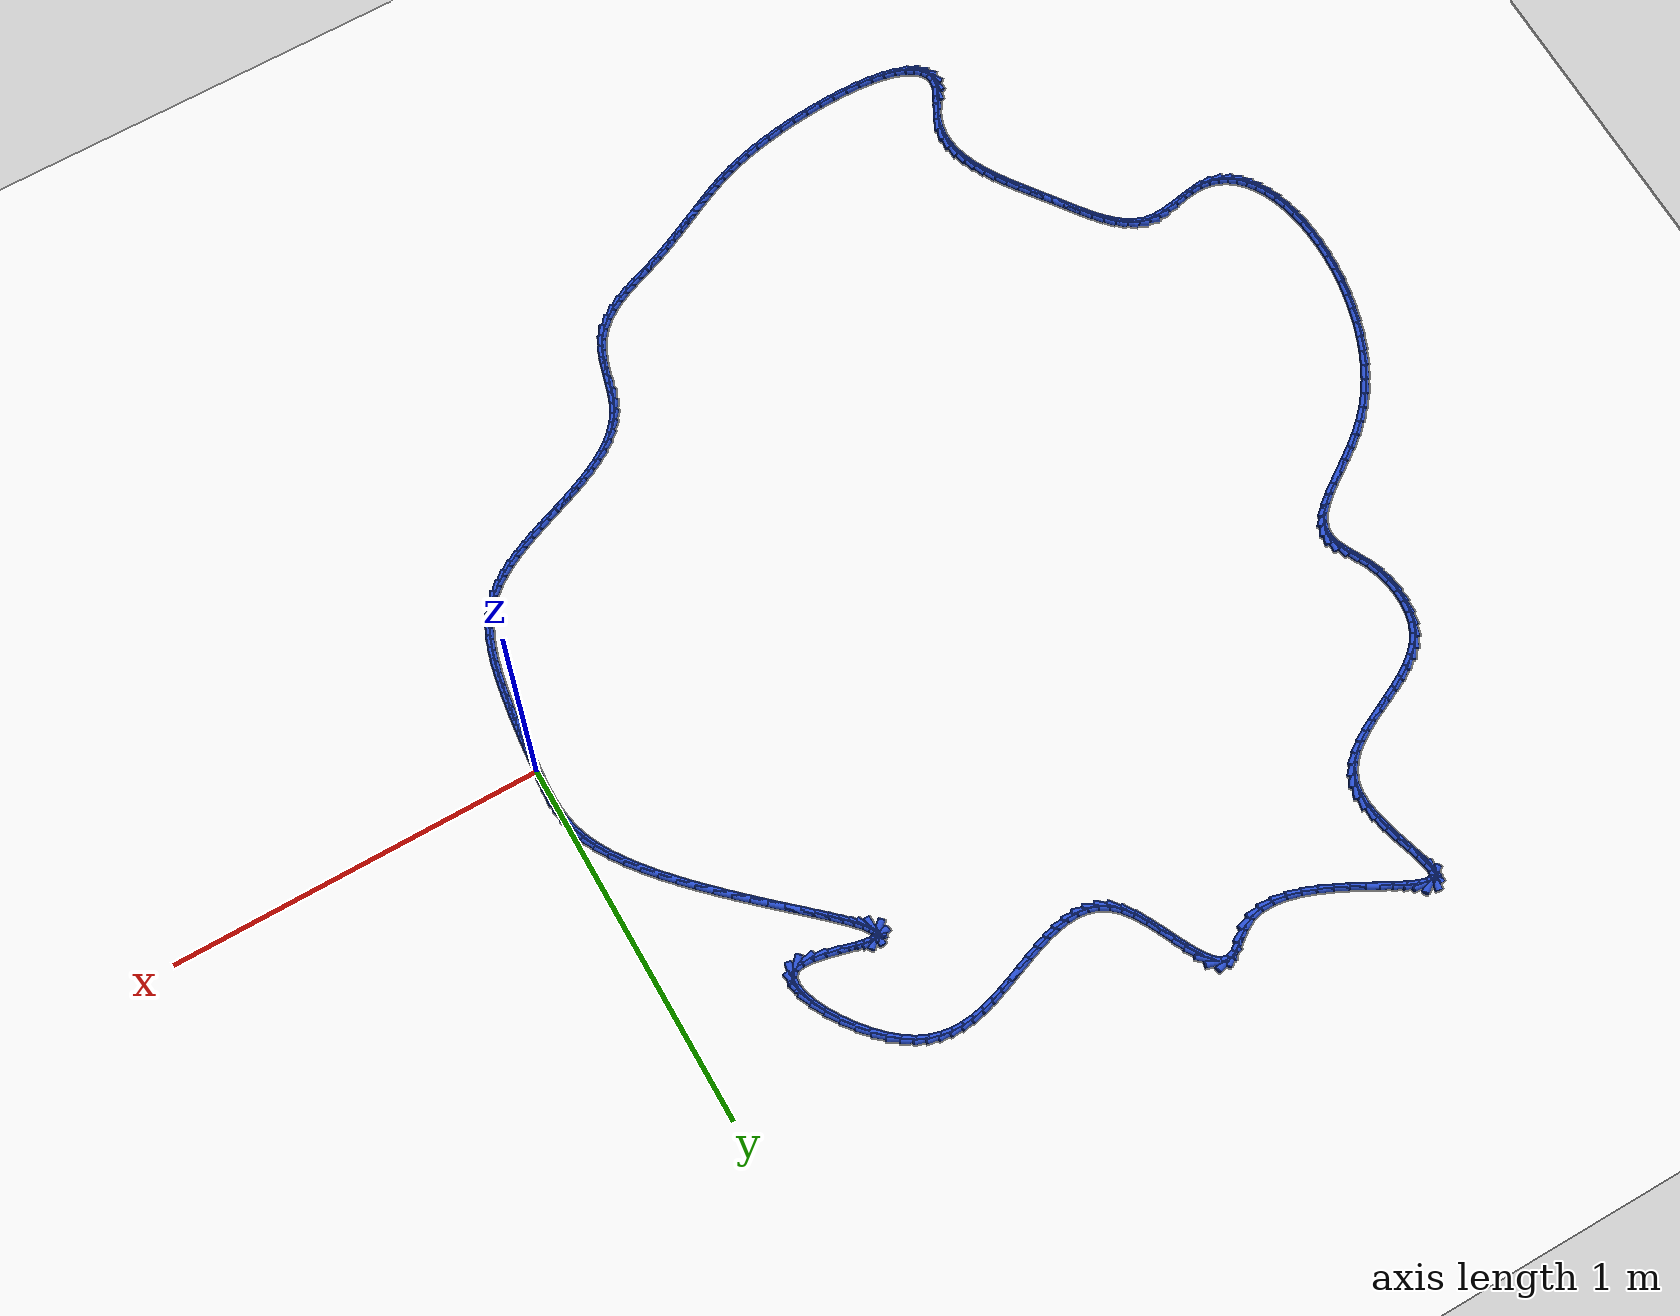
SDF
<sdf version="1.6">
 <world name="default">
  <light name="sun" type="directional">
   <pose>0 0 10 0 -0 0</pose>
   <diffuse>0.8 0.8 0.8 1</diffuse>
   <specular>0.2 0.2 0.2 1</specular>
   <attenuation>
    <range>1000</range>
    <constant>0.9</constant>
    <linear>0.01</linear>
    <quadratic>0.001</quadratic>
   </attenuation>
   <direction>-0.5 0.1 -0.9</direction>
  </light>
  <model name="ground_plane">
   <static>1</static>
   <link name="link">
    <collision name="collision">
     <geometry><plane><normal>0 0 1</normal><size>100 100</size></plane></geometry>
     <surface><friction><ode><mu>100</mu><mu2>50</mu2></ode></friction></surface>
    </collision>
    <visual name="visual">
     <cast_shadows>0</cast_shadows>
     <geometry><plane><normal>0 0 1</normal><size>100 100</size></plane></geometry>
     <material>
      <script><uri>file://media/materials/scripts/gazebo.material</uri><name>Gazebo/WhiteGlow</name></script>
     </material>
    </visual>
   </link>
  </model>
  <gravity>0 0 -9.8</gravity>
  <magnetic_field>6e-06 2.3e-05 -4.2e-05</magnetic_field>
  <atmosphere type="adiabatic"/>
  <physics name="default_physics" default="0" type="ode">
   <max_step_size>0.001</max_step_size>
   <real_time_factor>1</real_time_factor>
   <real_time_update_rate>1000</real_time_update_rate>
  </physics>
  <scene><ambient>0.4 0.4 0.4 1</ambient><background>0.7 0.7 0.7 1</background><shadows>1</shadows></scene>
  <spherical_coordinates>
   <surface_model>EARTH_WGS84</surface_model>
   <latitude_deg>0</latitude_deg>
   <longitude_deg>0</longitude_deg>
   <elevation>0</elevation>
   <heading_deg>0</heading_deg>
  </spherical_coordinates>
  <model name="line">
   <link name="link_0">
    <pose>2.8189256484623115e-17 0.0 0.01 0 1.57 1.494889805326992</pose>
    <collision name="collision">
     <geometry><cylinder><radius>0.01</radius><length>0.08</length></cylinder></geometry>
    </collision>
    <visual name="visual">
     <material>
      <script><name>Gazebo/Blue</name><uri>file://media/materials/scripts/gazebo.material</uri></script>
     </material>
     <geometry><cylinder><radius>0.01</radius><length>0.08</length></cylinder></geometry>
    </visual>
   </link>
   <link name="link_1">
    <pose>0.0022317643010857065 0.029344992816487968 0.01 0 1.57 1.518458784926775</pose>
    <collision name="collision">
     <geometry><cylinder><radius>0.01</radius><length>0.08</length></cylinder></geometry>
    </collision>
    <visual name="visual">
     <material>
      <script><name>Gazebo/Blue</name><uri>file://media/materials/scripts/gazebo.material</uri></script>
     </material>
     <geometry><cylinder><radius>0.01</radius><length>0.08</length></cylinder></geometry>
    </visual>
   </link>
   <link name="link_2">
    <pose>0.0037677922287442937 0.058666682590855446 0.01 0 1.57 1.5623826022286036</pose>
    <collision name="collision">
     <geometry><cylinder><radius>0.01</radius><length>0.08</length></cylinder></geometry>
    </collision>
    <visual name="visual">
     <material>
      <script><name>Gazebo/Blue</name><uri>file://media/materials/scripts/gazebo.material</uri></script>
     </material>
     <geometry><cylinder><radius>0.01</radius><length>0.08</length></cylinder></geometry>
    </visual>
   </link>
   <link name="link_3">
    <pose>0.004015538080015707 0.08811143125747996 0.01 0 1.57 -1.5158918603189455</pose>
    <collision name="collision">
     <geometry><cylinder><radius>0.01</radius><length>0.08</length></cylinder></geometry>
    </collision>
    <visual name="visual">
     <material>
      <script><name>Gazebo/Blue</name><uri>file://media/materials/scripts/gazebo.material</uri></script>
     </material>
     <geometry><cylinder><radius>0.01</radius><length>0.08</length></cylinder></geometry>
    </visual>
   </link>
   <link name="link_4">
    <pose>0.0023824561519398537 0.11782560075073899 0.01 0 1.57 -1.4353394648097961</pose>
    <collision name="collision">
     <geometry><cylinder><radius>0.01</radius><length>0.08</length></cylinder></geometry>
    </collision>
    <visual name="visual">
     <material>
      <script><name>Gazebo/Blue</name><uri>file://media/materials/scripts/gazebo.material</uri></script>
     </material>
     <geometry><cylinder><radius>0.01</radius><length>0.08</length></cylinder></geometry>
    </visual>
   </link>
   <link name="link_5">
    <pose>-0.0017239992584433435 0.14795555300501012 0.01 0 1.57 -1.3412280706990383</pose>
    <collision name="collision">
     <geometry><cylinder><radius>0.01</radius><length>0.08</length></cylinder></geometry>
    </collision>
    <visual name="visual">
     <material>
      <script><name>Gazebo/Blue</name><uri>file://media/materials/scripts/gazebo.material</uri></script>
     </material>
     <geometry><cylinder><radius>0.01</radius><length>0.08</length></cylinder></geometry>
    </visual>
   </link>
   <link name="link_6">
    <pose>-0.008896373854093979 0.1786476499546708 0.01 0 1.57 -1.2386501903018092</pose>
    <collision name="collision">
     <geometry><cylinder><radius>0.01</radius><length>0.08</length></cylinder></geometry>
    </collision>
    <visual name="visual">
     <material>
      <script><name>Gazebo/Blue</name><uri>file://media/materials/scripts/gazebo.material</uri></script>
     </material>
     <geometry><cylinder><radius>0.01</radius><length>0.08</length></cylinder></geometry>
    </visual>
   </link>
   <link name="link_7">
    <pose>-0.01972721333797213 0.21004825353409845 0.01 0 1.57 -1.1343315740553832</pose>
    <collision name="collision">
     <geometry><cylinder><radius>0.01</radius><length>0.08</length></cylinder></geometry>
    </collision>
    <visual name="visual">
     <material>
      <script><name>Gazebo/Blue</name><uri>file://media/materials/scripts/gazebo.material</uri></script>
     </material>
     <geometry><cylinder><radius>0.01</radius><length>0.08</length></cylinder></geometry>
    </visual>
   </link>
   <link name="link_8">
    <pose>-0.034767137621708605 0.24229032603372597 0.01 0 1.57 -1.04424895788949</pose>
    <collision name="collision">
     <geometry><cylinder><radius>0.01</radius><length>0.08</length></cylinder></geometry>
    </collision>
    <visual name="visual">
     <material>
      <script><name>Gazebo/Blue</name><uri>file://media/materials/scripts/gazebo.material</uri></script>
     </material>
     <geometry><cylinder><radius>0.01</radius><length>0.08</length></cylinder></geometry>
    </visual>
   </link>
   <link name="link_9">
    <pose>-0.05396341555243429 0.275313996426315 0.01 0 1.57 -0.9736424970683031</pose>
    <collision name="collision">
     <geometry><cylinder><radius>0.01</radius><length>0.08</length></cylinder></geometry>
    </collision>
    <visual name="visual">
     <material>
      <script><name>Gazebo/Blue</name><uri>file://media/materials/scripts/gazebo.material</uri></script>
     </material>
     <geometry><cylinder><radius>0.01</radius><length>0.08</length></cylinder></geometry>
    </visual>
   </link>
   <link name="link_10">
    <pose>-0.07681082350426537 0.3089147753522391 0.01 0 1.57 -0.9178499734605542</pose>
    <collision name="collision">
     <geometry><cylinder><radius>0.01</radius><length>0.08</length></cylinder></geometry>
    </collision>
    <visual name="visual">
     <material>
      <script><name>Gazebo/Blue</name><uri>file://media/materials/scripts/gazebo.material</uri></script>
     </material>
     <geometry><cylinder><radius>0.01</radius><length>0.08</length></cylinder></geometry>
    </visual>
   </link>
   <link name="link_11">
    <pose>-0.10279316896690821 0.3428846677542832 0.01 0 1.57 -0.8733222555795672</pose>
    <collision name="collision">
     <geometry><cylinder><radius>0.01</radius><length>0.08</length></cylinder></geometry>
    </collision>
    <visual name="visual">
     <material>
      <script><name>Gazebo/Blue</name><uri>file://media/materials/scripts/gazebo.material</uri></script>
     </material>
     <geometry><cylinder><radius>0.01</radius><length>0.08</length></cylinder></geometry>
    </visual>
   </link>
   <link name="link_12">
    <pose>-0.13139425943006916 0.3770156785752323 0.01 0 1.57 -0.8375288050863591</pose>
    <collision name="collision">
     <geometry><cylinder><radius>0.01</radius><length>0.08</length></cylinder></geometry>
    </collision>
    <visual name="visual">
     <material>
      <script><name>Gazebo/Blue</name><uri>file://media/materials/scripts/gazebo.material</uri></script>
     </material>
     <geometry><cylinder><radius>0.01</radius><length>0.08</length></cylinder></geometry>
    </visual>
   </link>
   <link name="link_13">
    <pose>-0.16209790238345462 0.4110998127578713 0.01 0 1.57 -0.8086740053437779</pose>
    <collision name="collision">
     <geometry><cylinder><radius>0.01</radius><length>0.08</length></cylinder></geometry>
    </collision>
    <visual name="visual">
     <material>
      <script><name>Gazebo/Blue</name><uri>file://media/materials/scripts/gazebo.material</uri></script>
     </material>
     <geometry><cylinder><radius>0.01</radius><length>0.08</length></cylinder></geometry>
    </visual>
   </link>
   <link name="link_14">
    <pose>-0.19438790531677103 0.44492907524498543 0.01 0 1.57 -0.7854914595426359</pose>
    <collision name="collision">
     <geometry><cylinder><radius>0.01</radius><length>0.08</length></cylinder></geometry>
    </collision>
    <visual name="visual">
     <material>
      <script><name>Gazebo/Blue</name><uri>file://media/materials/scripts/gazebo.material</uri></script>
     </material>
     <geometry><cylinder><radius>0.01</radius><length>0.08</length></cylinder></geometry>
    </visual>
   </link>
   <link name="link_15">
    <pose>-0.22774807571972458 0.47829547097935926 0.01 0 1.57 -0.767105393911474</pose>
    <collision name="collision">
     <geometry><cylinder><radius>0.01</radius><length>0.08</length></cylinder></geometry>
    </collision>
    <visual name="visual">
     <material>
      <script><name>Gazebo/Blue</name><uri>file://media/materials/scripts/gazebo.material</uri></script>
     </material>
     <geometry><cylinder><radius>0.01</radius><length>0.08</length></cylinder></geometry>
    </visual>
   </link>
   <link name="link_16">
    <pose>-0.26166222108202186 0.510991004903778 0.01 0 1.57 -0.7529434532309567</pose>
    <collision name="collision">
     <geometry><cylinder><radius>0.01</radius><length>0.08</length></cylinder></geometry>
    </collision>
    <visual name="visual">
     <material>
      <script><name>Gazebo/Blue</name><uri>file://media/materials/scripts/gazebo.material</uri></script>
     </material>
     <geometry><cylinder><radius>0.01</radius><length>0.08</length></cylinder></geometry>
    </visual>
   </link>
   <link name="link_17">
    <pose>-0.2956141488933692 0.5428076819610268 0.01 0 1.57 -0.7426897292777561</pose>
    <collision name="collision">
     <geometry><cylinder><radius>0.01</radius><length>0.08</length></cylinder></geometry>
    </collision>
    <visual name="visual">
     <material>
      <script><name>Gazebo/Blue</name><uri>file://media/materials/scripts/gazebo.material</uri></script>
     </material>
     <geometry><cylinder><radius>0.01</radius><length>0.08</length></cylinder></geometry>
    </visual>
   </link>
   <link name="link_18">
    <pose>-0.32908766664347294 0.5735375070938905 0.01 0 1.57 -0.7362736791888564</pose>
    <collision name="collision">
     <geometry><cylinder><radius>0.01</radius><length>0.08</length></cylinder></geometry>
    </collision>
    <visual name="visual">
     <material>
      <script><name>Gazebo/Blue</name><uri>file://media/materials/scripts/gazebo.material</uri></script>
     </material>
     <geometry><cylinder><radius>0.01</radius><length>0.08</length></cylinder></geometry>
    </visual>
   </link>
   <link name="link_19">
    <pose>-0.3615665818220395 0.6029724852451539 0.01 0 1.57 -0.733899243789681</pose>
    <collision name="collision">
     <geometry><cylinder><radius>0.01</radius><length>0.08</length></cylinder></geometry>
    </collision>
    <visual name="visual">
     <material>
      <script><name>Gazebo/Blue</name><uri>file://media/materials/scripts/gazebo.material</uri></script>
     </material>
     <geometry><cylinder><radius>0.01</radius><length>0.08</length></cylinder></geometry>
    </visual>
   </link>
   <link name="link_20">
    <pose>-0.3925347019187752 0.6309046213576021 0.01 0 1.57 -0.7361321577931114</pose>
    <collision name="collision">
     <geometry><cylinder><radius>0.01</radius><length>0.08</length></cylinder></geometry>
    </collision>
    <visual name="visual">
     <material>
      <script><name>Gazebo/Blue</name><uri>file://media/materials/scripts/gazebo.material</uri></script>
     </material>
     <geometry><cylinder><radius>0.01</radius><length>0.08</length></cylinder></geometry>
    </visual>
   </link>
   <link name="link_21">
    <pose>-0.4214758344233865 0.6571259203740201 0.01 0 1.57 -0.7440909394986537</pose>
    <collision name="collision">
     <geometry><cylinder><radius>0.01</radius><length>0.08</length></cylinder></geometry>
    </collision>
    <visual name="visual">
     <material>
      <script><name>Gazebo/Blue</name><uri>file://media/materials/scripts/gazebo.material</uri></script>
     </material>
     <geometry><cylinder><radius>0.01</radius><length>0.08</length></cylinder></geometry>
    </visual>
   </link>
   <link name="link_22">
    <pose>-0.44787378682557955 0.6814283872371926 0.01 0 1.57 -0.7598525828995999</pose>
    <collision name="collision">
     <geometry><cylinder><radius>0.01</radius><length>0.08</length></cylinder></geometry>
    </collision>
    <visual name="visual">
     <material>
      <script><name>Gazebo/Blue</name><uri>file://media/materials/scripts/gazebo.material</uri></script>
     </material>
     <geometry><cylinder><radius>0.01</radius><length>0.08</length></cylinder></geometry>
    </visual>
   </link>
   <link name="link_23">
    <pose>-0.47121236661506116 0.7036040268899051 0.01 0 1.57 -0.7873626858802841</pose>
    <collision name="collision">
     <geometry><cylinder><radius>0.01</radius><length>0.08</length></cylinder></geometry>
    </collision>
    <visual name="visual">
     <material>
      <script><name>Gazebo/Blue</name><uri>file://media/materials/scripts/gazebo.material</uri></script>
     </material>
     <geometry><cylinder><radius>0.01</radius><length>0.08</length></cylinder></geometry>
    </visual>
   </link>
   <link name="link_24">
    <pose>-0.49097538128153717 0.723444844274942 0.01 0 1.57 -0.8346993901617263</pose>
    <collision name="collision">
     <geometry><cylinder><radius>0.01</radius><length>0.08</length></cylinder></geometry>
    </collision>
    <visual name="visual">
     <material>
      <script><name>Gazebo/Blue</name><uri>file://media/materials/scripts/gazebo.material</uri></script>
     </material>
     <geometry><cylinder><radius>0.01</radius><length>0.08</length></cylinder></geometry>
    </visual>
   </link>
   <link name="link_25">
    <pose>-0.5066466383147146 0.740742844335089 0.01 0 1.57 -0.920601583920619</pose>
    <collision name="collision">
     <geometry><cylinder><radius>0.01</radius><length>0.08</length></cylinder></geometry>
    </collision>
    <visual name="visual">
     <material>
      <script><name>Gazebo/Blue</name><uri>file://media/materials/scripts/gazebo.material</uri></script>
     </material>
     <geometry><cylinder><radius>0.01</radius><length>0.08</length></cylinder></geometry>
    </visual>
   </link>
   <link name="link_26">
    <pose>-0.517709945204299 0.75529003201313 0.01 0 1.57 -1.0971906398215314</pose>
    <collision name="collision">
     <geometry><cylinder><radius>0.01</radius><length>0.08</length></cylinder></geometry>
    </collision>
    <visual name="visual">
     <material>
      <script><name>Gazebo/Blue</name><uri>file://media/materials/scripts/gazebo.material</uri></script>
     </material>
     <geometry><cylinder><radius>0.01</radius><length>0.08</length></cylinder></geometry>
    </visual>
   </link>
   <link name="link_27">
    <pose>-0.5236491094399977 0.7668784122518512 0.01 0 1.57 -1.5353274684425158</pose>
    <collision name="collision">
     <geometry><cylinder><radius>0.01</radius><length>0.08</length></cylinder></geometry>
    </collision>
    <visual name="visual">
     <material>
      <script><name>Gazebo/Blue</name><uri>file://media/materials/scripts/gazebo.material</uri></script>
     </material>
     <geometry><cylinder><radius>0.01</radius><length>0.08</length></cylinder></geometry>
    </visual>
   </link>
   <link name="link_28">
    <pose>-0.5239479385115163 0.7752999899940368 0.01 0 1.57 0.7111691689588562</pose>
    <collision name="collision">
     <geometry><cylinder><radius>0.01</radius><length>0.08</length></cylinder></geometry>
    </collision>
    <visual name="visual">
     <material>
      <script><name>Gazebo/Blue</name><uri>file://media/materials/scripts/gazebo.material</uri></script>
     </material>
     <geometry><cylinder><radius>0.01</radius><length>0.08</length></cylinder></geometry>
    </visual>
   </link>
   <link name="link_29">
    <pose>-0.5180902399085616 0.780346770182472 0.01 0 1.57 0.11630738938080655</pose>
    <collision name="collision">
     <geometry><cylinder><radius>0.01</radius><length>0.08</length></cylinder></geometry>
    </collision>
    <visual name="visual">
     <material>
      <script><name>Gazebo/Blue</name><uri>file://media/materials/scripts/gazebo.material</uri></script>
     </material>
     <geometry><cylinder><radius>0.01</radius><length>0.08</length></cylinder></geometry>
    </visual>
   </link>
   <link name="link_30">
    <pose>-0.50555982112084 0.7818107577599416 0.01 0 1.57 -0.11745280071256992</pose>
    <collision name="collision">
     <geometry><cylinder><radius>0.01</radius><length>0.08</length></cylinder></geometry>
    </collision>
    <visual name="visual">
     <material>
      <script><name>Gazebo/Blue</name><uri>file://media/materials/scripts/gazebo.material</uri></script>
     </material>
     <geometry><cylinder><radius>0.01</radius><length>0.08</length></cylinder></geometry>
    </visual>
   </link>
   <link name="link_31">
    <pose>-0.4858404896380576 0.779483957669231 0.01 0 1.57 -0.2210084833847514</pose>
    <collision name="collision">
     <geometry><cylinder><radius>0.01</radius><length>0.08</length></cylinder></geometry>
    </collision>
    <visual name="visual">
     <material>
      <script><name>Gazebo/Blue</name><uri>file://media/materials/scripts/gazebo.material</uri></script>
     </material>
     <geometry><cylinder><radius>0.01</radius><length>0.08</length></cylinder></geometry>
    </visual>
   </link>
   <link name="link_32">
    <pose>-0.4587817184295532 0.7734044315404087 0.01 0 1.57 -0.2501404502065189</pose>
    <collision name="collision">
     <geometry><cylinder><radius>0.01</radius><length>0.08</length></cylinder></geometry>
    </collision>
    <visual name="visual">
     <material>
      <script><name>Gazebo/Blue</name><uri>file://media/materials/scripts/gazebo.material</uri></script>
     </material>
     <geometry><cylinder><radius>0.01</radius><length>0.08</length></cylinder></geometry>
    </visual>
   </link>
   <link name="link_33">
    <pose>-0.4265503221247066 0.7651695826530442 0.01 0 1.57 -0.2340038350483823</pose>
    <collision name="collision">
     <geometry><cylinder><radius>0.01</radius><length>0.08</length></cylinder></geometry>
    </collision>
    <visual name="visual">
     <material>
      <script><name>Gazebo/Blue</name><uri>file://media/materials/scripts/gazebo.material</uri></script>
     </material>
     <geometry><cylinder><radius>0.01</radius><length>0.08</length></cylinder></geometry>
    </visual>
   </link>
   <link name="link_34">
    <pose>-0.3922181182099734 0.7569857916646607 0.01 0 1.57 -0.17577822024683615</pose>
    <collision name="collision">
     <geometry><cylinder><radius>0.01</radius><length>0.08</length></cylinder></geometry>
    </collision>
    <visual name="visual">
     <material>
      <script><name>Gazebo/Blue</name><uri>file://media/materials/scripts/gazebo.material</uri></script>
     </material>
     <geometry><cylinder><radius>0.01</radius><length>0.08</length></cylinder></geometry>
    </visual>
   </link>
   <link name="link_35">
    <pose>-0.3588590000979135 0.7510608361256487 0.01 0 1.57 -0.049711181442765685</pose>
    <collision name="collision">
     <geometry><cylinder><radius>0.01</radius><length>0.08</length></cylinder></geometry>
    </collision>
    <visual name="visual">
     <material>
      <script><name>Gazebo/Blue</name><uri>file://media/materials/scripts/gazebo.material</uri></script>
     </material>
     <geometry><cylinder><radius>0.01</radius><length>0.08</length></cylinder></geometry>
    </visual>
   </link>
   <link name="link_36">
    <pose>-0.3295468612010875 0.7496024935863989 0.01 0 1.57 0.23085373428212153</pose>
    <collision name="collision">
     <geometry><cylinder><radius>0.01</radius><length>0.08</length></cylinder></geometry>
    </collision>
    <visual name="visual">
     <material>
      <script><name>Gazebo/Blue</name><uri>file://media/materials/scripts/gazebo.material</uri></script>
     </material>
     <geometry><cylinder><radius>0.01</radius><length>0.08</length></cylinder></geometry>
    </visual>
   </link>
   <link name="link_37">
    <pose>-0.3073554871068196 0.7548184447226095 0.01 0 1.57 0.806841206505881</pose>
    <collision name="collision">
     <geometry><cylinder><radius>0.01</radius><length>0.08</length></cylinder></geometry>
    </collision>
    <visual name="visual">
     <material>
      <script><name>Gazebo/Blue</name><uri>file://media/materials/scripts/gazebo.material</uri></script>
     </material>
     <geometry><cylinder><radius>0.01</radius><length>0.08</length></cylinder></geometry>
    </visual>
   </link>
   <link name="link_38">
    <pose>-0.2945476305047943 0.7681877044053672 0.01 0 1.57 1.3818599184849405</pose>
    <collision name="collision">
     <geometry><cylinder><radius>0.01</radius><length>0.08</length></cylinder></geometry>
    </collision>
    <visual name="visual">
     <material>
      <script><name>Gazebo/Blue</name><uri>file://media/materials/scripts/gazebo.material</uri></script>
     </material>
     <geometry><cylinder><radius>0.01</radius><length>0.08</length></cylinder></geometry>
    </visual>
   </link>
   <link name="link_39">
    <pose>-0.29062386848283916 0.7887076336625384 0.01 0 1.57 -1.4236883605855977</pose>
    <collision name="collision">
     <geometry><cylinder><radius>0.01</radius><length>0.08</length></cylinder></geometry>
    </collision>
    <visual name="visual">
     <material>
      <script><name>Gazebo/Blue</name><uri>file://media/materials/scripts/gazebo.material</uri></script>
     </material>
     <geometry><cylinder><radius>0.01</radius><length>0.08</length></cylinder></geometry>
    </visual>
   </link>
   <link name="link_40">
    <pose>-0.2944972695206044 0.8148477512680685 0.01 0 1.57 -1.2340273860745257</pose>
    <collision name="collision">
     <geometry><cylinder><radius>0.01</radius><length>0.08</length></cylinder></geometry>
    </collision>
    <visual name="visual">
     <material>
      <script><name>Gazebo/Blue</name><uri>file://media/materials/scripts/gazebo.material</uri></script>
     </material>
     <geometry><cylinder><radius>0.01</radius><length>0.08</length></cylinder></geometry>
    </visual>
   </link>
   <link name="link_41">
    <pose>-0.3050809020977397 0.8450775759959032 0.01 0 1.57 -1.111736143907085</pose>
    <collision name="collision">
     <geometry><cylinder><radius>0.01</radius><length>0.08</length></cylinder></geometry>
    </collision>
    <visual name="visual">
     <material>
      <script><name>Gazebo/Blue</name><uri>file://media/materials/scripts/gazebo.material</uri></script>
     </material>
     <geometry><cylinder><radius>0.01</radius><length>0.08</length></cylinder></geometry>
    </visual>
   </link>
   <link name="link_42">
    <pose>-0.32128783469389494 0.8778666266199875 0.01 0 1.57 -1.02059358967457</pose>
    <collision name="collision">
     <geometry><cylinder><radius>0.01</radius><length>0.08</length></cylinder></geometry>
    </collision>
    <visual name="visual">
     <material>
      <script><name>Gazebo/Blue</name><uri>file://media/materials/scripts/gazebo.material</uri></script>
     </material>
     <geometry><cylinder><radius>0.01</radius><length>0.08</length></cylinder></geometry>
    </visual>
   </link>
   <link name="link_43">
    <pose>-0.3420311357887203 0.911684421914267 0.01 0 1.57 -0.9427292144932088</pose>
    <collision name="collision">
     <geometry><cylinder><radius>0.01</radius><length>0.08</length></cylinder></geometry>
    </collision>
    <visual name="visual">
     <material>
      <script><name>Gazebo/Blue</name><uri>file://media/materials/scripts/gazebo.material</uri></script>
     </material>
     <geometry><cylinder><radius>0.01</radius><length>0.08</length></cylinder></geometry>
    </visual>
   </link>
   <link name="link_44">
    <pose>-0.3662238738618657 0.9450004806526877 0.01 0 1.57 -0.8669711093233123</pose>
    <collision name="collision">
     <geometry><cylinder><radius>0.01</radius><length>0.08</length></cylinder></geometry>
    </collision>
    <visual name="visual">
     <material>
      <script><name>Gazebo/Blue</name><uri>file://media/materials/scripts/gazebo.material</uri></script>
     </material>
     <geometry><cylinder><radius>0.01</radius><length>0.08</length></cylinder></geometry>
    </visual>
   </link>
   <link name="link_45">
    <pose>-0.3927791173929808 0.9762843216091943 0.01 0 1.57 -0.7834238788024632</pose>
    <collision name="collision">
     <geometry><cylinder><radius>0.01</radius><length>0.08</length></cylinder></geometry>
    </collision>
    <visual name="visual">
     <material>
      <script><name>Gazebo/Blue</name><uri>file://media/materials/scripts/gazebo.material</uri></script>
     </material>
     <geometry><cylinder><radius>0.01</radius><length>0.08</length></cylinder></geometry>
    </visual>
   </link>
   <link name="link_46">
    <pose>-0.42060993486171594 1.004005463557733 0.01 0 1.57 -0.68135008948826</pose>
    <collision name="collision">
     <geometry><cylinder><radius>0.01</radius><length>0.08</length></cylinder></geometry>
    </collision>
    <visual name="visual">
     <material>
      <script><name>Gazebo/Blue</name><uri>file://media/materials/scripts/gazebo.material</uri></script>
     </material>
     <geometry><cylinder><radius>0.01</radius><length>0.08</length></cylinder></geometry>
    </visual>
   </link>
   <link name="link_47">
    <pose>-0.4487565725889073 1.0268294813146133 0.01 0 1.57 -0.5614868905433444</pose>
    <collision name="collision">
     <geometry><cylinder><radius>0.01</radius><length>0.08</length></cylinder></geometry>
    </collision>
    <visual name="visual">
     <material>
      <script><name>Gazebo/Blue</name><uri>file://media/materials/scripts/gazebo.material</uri></script>
     </material>
     <geometry><cylinder><radius>0.01</radius><length>0.08</length></cylinder></geometry>
    </visual>
   </link>
   <link name="link_48">
    <pose>-0.4770344089896217 1.044616885301963 0.01 0 1.57 -0.42951385783106766</pose>
    <collision name="collision">
     <geometry><cylinder><radius>0.01</radius><length>0.08</length></cylinder></geometry>
    </collision>
    <visual name="visual">
     <material>
      <script><name>Gazebo/Blue</name><uri>file://media/materials/scripts/gazebo.material</uri></script>
     </material>
     <geometry><cylinder><radius>0.01</radius><length>0.08</length></cylinder></geometry>
    </visual>
   </link>
   <link name="link_49">
    <pose>-0.5055508287335735 1.0576783397587843 0.01 0 1.57 -0.29107896437109526</pose>
    <collision name="collision">
     <geometry><cylinder><radius>0.01</radius><length>0.08</length></cylinder></geometry>
    </collision>
    <visual name="visual">
     <material>
      <script><name>Gazebo/Blue</name><uri>file://media/materials/scripts/gazebo.material</uri></script>
     </material>
     <geometry><cylinder><radius>0.01</radius><length>0.08</length></cylinder></geometry>
    </visual>
   </link>
   <link name="link_50">
    <pose>-0.5344137494787723 1.0663253305733127 0.01 0 1.57 -0.15377048607688243</pose>
    <collision name="collision">
     <geometry><cylinder><radius>0.01</radius><length>0.08</length></cylinder></geometry>
    </collision>
    <visual name="visual">
     <material>
      <script><name>Gazebo/Blue</name><uri>file://media/materials/scripts/gazebo.material</uri></script>
     </material>
     <geometry><cylinder><radius>0.01</radius><length>0.08</length></cylinder></geometry>
    </visual>
   </link>
   <link name="link_51">
    <pose>-0.5637310888832271 1.070869343633784 0.01 0 1.57 -0.025179729439198904</pose>
    <collision name="collision">
     <geometry><cylinder><radius>0.01</radius><length>0.08</length></cylinder></geometry>
    </collision>
    <visual name="visual">
     <material>
      <script><name>Gazebo/Blue</name><uri>file://media/materials/scripts/gazebo.material</uri></script>
     </material>
     <geometry><cylinder><radius>0.01</radius><length>0.08</length></cylinder></geometry>
    </visual>
   </link>
   <link name="link_52">
    <pose>-0.5936107646049474 1.0716218648284324 0.01 0 1.57 0.08904349330686956</pose>
    <collision name="collision">
     <geometry><cylinder><radius>0.01</radius><length>0.08</length></cylinder></geometry>
    </collision>
    <visual name="visual">
     <material>
      <script><name>Gazebo/Blue</name><uri>file://media/materials/scripts/gazebo.material</uri></script>
     </material>
     <geometry><cylinder><radius>0.01</radius><length>0.08</length></cylinder></geometry>
    </visual>
   </link>
   <link name="link_53">
    <pose>-0.6241606943019424 1.0688943800454949 0.01 0 1.57 0.18585548429169674</pose>
    <collision name="collision">
     <geometry><cylinder><radius>0.01</radius><length>0.08</length></cylinder></geometry>
    </collision>
    <visual name="visual">
     <material>
      <script><name>Gazebo/Blue</name><uri>file://media/materials/scripts/gazebo.material</uri></script>
     </material>
     <geometry><cylinder><radius>0.01</radius><length>0.08</length></cylinder></geometry>
    </visual>
   </link>
   <link name="link_54">
    <pose>-0.6554833786266323 1.0630049189397592 0.01 0 1.57 0.26089669984190533</pose>
    <collision name="collision">
     <geometry><cylinder><radius>0.01</radius><length>0.08</length></cylinder></geometry>
    </collision>
    <visual name="visual">
     <material>
      <script><name>Gazebo/Blue</name><uri>file://media/materials/scripts/gazebo.material</uri></script>
     </material>
     <geometry><cylinder><radius>0.01</radius><length>0.08</length></cylinder></geometry>
    </visual>
   </link>
   <link name="link_55">
    <pose>-0.6875355833711626 1.0544475595175822 0.01 0 1.57 0.31287571941182585</pose>
    <collision name="collision">
     <geometry><cylinder><radius>0.01</radius><length>0.08</length></cylinder></geometry>
    </collision>
    <visual name="visual">
     <material>
      <script><name>Gazebo/Blue</name><uri>file://media/materials/scripts/gazebo.material</uri></script>
     </material>
     <geometry><cylinder><radius>0.01</radius><length>0.08</length></cylinder></geometry>
    </visual>
   </link>
   <link name="link_56">
    <pose>-0.7201155248386961 1.043907908264675 0.01 0 1.57 0.345109959659333</pose>
    <collision name="collision">
     <geometry><cylinder><radius>0.01</radius><length>0.08</length></cylinder></geometry>
    </collision>
    <visual name="visual">
     <material>
      <script><name>Gazebo/Blue</name><uri>file://media/materials/scripts/gazebo.material</uri></script>
     </material>
     <geometry><cylinder><radius>0.01</radius><length>0.08</length></cylinder></geometry>
    </visual>
   </link>
   <link name="link_57">
    <pose>-0.7530134336931754 1.0320812183540145 0.01 0 1.57 0.35986419046383605</pose>
    <collision name="collision">
     <geometry><cylinder><radius>0.01</radius><length>0.08</length></cylinder></geometry>
    </collision>
    <visual name="visual">
     <material>
      <script><name>Gazebo/Blue</name><uri>file://media/materials/scripts/gazebo.material</uri></script>
     </material>
     <geometry><cylinder><radius>0.01</radius><length>0.08</length></cylinder></geometry>
    </visual>
   </link>
   <link name="link_58">
    <pose>-0.7860195405985431 1.0196627429585778 0.01 0 1.57 0.3581259093521344</pose>
    <collision name="collision">
     <geometry><cylinder><radius>0.01</radius><length>0.08</length></cylinder></geometry>
    </collision>
    <visual name="visual">
     <material>
      <script><name>Gazebo/Blue</name><uri>file://media/materials/scripts/gazebo.material</uri></script>
     </material>
     <geometry><cylinder><radius>0.01</radius><length>0.08</length></cylinder></geometry>
    </visual>
   </link>
   <link name="link_59">
    <pose>-0.8189240762187421 1.007347735251343 0.01 0 1.57 0.33964196082103437</pose>
    <collision name="collision">
     <geometry><cylinder><radius>0.01</radius><length>0.08</length></cylinder></geometry>
    </collision>
    <visual name="visual">
     <material>
      <script><name>Gazebo/Blue</name><uri>file://media/materials/scripts/gazebo.material</uri></script>
     </material>
     <geometry><cylinder><radius>0.01</radius><length>0.08</length></cylinder></geometry>
    </visual>
   </link>
   <link name="link_60">
    <pose>-0.8515172712177145 0.9958314484052864 0.01 0 1.57 0.3028787962446445</pose>
    <collision name="collision">
     <geometry><cylinder><radius>0.01</radius><length>0.08</length></cylinder></geometry>
    </collision>
    <visual name="visual">
     <material>
      <script><name>Gazebo/Blue</name><uri>file://media/materials/scripts/gazebo.material</uri></script>
     </material>
     <geometry><cylinder><radius>0.01</radius><length>0.08</length></cylinder></geometry>
    </visual>
   </link>
   <link name="link_61">
    <pose>-0.8835893562594037 0.9858091355933855 0.01 0 1.57 0.24491212057106673</pose>
    <collision name="collision">
     <geometry><cylinder><radius>0.01</radius><length>0.08</length></cylinder></geometry>
    </collision>
    <visual name="visual">
     <material>
      <script><name>Gazebo/Blue</name><uri>file://media/materials/scripts/gazebo.material</uri></script>
     </material>
     <geometry><cylinder><radius>0.01</radius><length>0.08</length></cylinder></geometry>
    </visual>
   </link>
   <link name="link_62">
    <pose>-0.9149305620077517 0.977976049988618 0.01 0 1.57 0.16136477019962725</pose>
    <collision name="collision">
     <geometry><cylinder><radius>0.01</radius><length>0.08</length></cylinder></geometry>
    </collision>
    <visual name="visual">
     <material>
      <script><name>Gazebo/Blue</name><uri>file://media/materials/scripts/gazebo.material</uri></script>
     </material>
     <geometry><cylinder><radius>0.01</radius><length>0.08</length></cylinder></geometry>
    </visual>
   </link>
   <link name="link_63">
    <pose>-0.945331119126702 0.9730274447639607 0.01 0 1.57 0.046764688557050176</pose>
    <collision name="collision">
     <geometry><cylinder><radius>0.01</radius><length>0.08</length></cylinder></geometry>
    </collision>
    <visual name="visual">
     <material>
      <script><name>Gazebo/Blue</name><uri>file://media/materials/scripts/gazebo.material</uri></script>
     </material>
     <geometry><cylinder><radius>0.01</radius><length>0.08</length></cylinder></geometry>
    </visual>
   </link>
   <link name="link_64">
    <pose>-0.9745812582801963 0.9716585730923908 0.01 0 1.57 -0.1038246799449227</pose>
    <collision name="collision">
     <geometry><cylinder><radius>0.01</radius><length>0.08</length></cylinder></geometry>
    </collision>
    <visual name="visual">
     <material>
      <script><name>Gazebo/Blue</name><uri>file://media/materials/scripts/gazebo.material</uri></script>
     </material>
     <geometry><cylinder><radius>0.01</radius><length>0.08</length></cylinder></geometry>
    </visual>
   </link>
   <link name="link_65">
    <pose>-1.0024712101321778 0.9745646881468858 0.01 0 1.57 -0.2907719402075284</pose>
    <collision name="collision">
     <geometry><cylinder><radius>0.01</radius><length>0.08</length></cylinder></geometry>
    </collision>
    <visual name="visual">
     <material>
      <script><name>Gazebo/Blue</name><uri>file://media/materials/scripts/gazebo.material</uri></script>
     </material>
     <geometry><cylinder><radius>0.01</radius><length>0.08</length></cylinder></geometry>
    </visual>
   </link>
   <link name="link_66">
    <pose>-1.028791205346589 0.9824410431004228 0.01 0 1.57 -0.5042405947862018</pose>
    <collision name="collision">
     <geometry><cylinder><radius>0.01</radius><length>0.08</length></cylinder></geometry>
    </collision>
    <visual name="visual">
     <material>
      <script><name>Gazebo/Blue</name><uri>file://media/materials/scripts/gazebo.material</uri></script>
     </material>
     <geometry><cylinder><radius>0.01</radius><length>0.08</length></cylinder></geometry>
    </visual>
   </link>
   <link name="link_67">
    <pose>-1.053331474587373 0.9959828911259789 0.01 0 1.57 -0.7230999425111835</pose>
    <collision name="collision">
     <geometry><cylinder><radius>0.01</radius><length>0.08</length></cylinder></geometry>
    </collision>
    <visual name="visual">
     <material>
      <script><name>Gazebo/Blue</name><uri>file://media/materials/scripts/gazebo.material</uri></script>
     </material>
     <geometry><cylinder><radius>0.01</radius><length>0.08</length></cylinder></geometry>
    </visual>
   </link>
   <link name="link_68">
    <pose>-1.0758822515608426 1.015885472570044 0.01 0 1.57 -0.9119410531576374</pose>
    <collision name="collision">
     <geometry><cylinder><radius>0.01</radius><length>0.08</length></cylinder></geometry>
    </collision>
    <visual name="visual">
     <material>
      <script><name>Gazebo/Blue</name><uri>file://media/materials/scripts/gazebo.material</uri></script>
     </material>
     <geometry><cylinder><radius>0.01</radius><length>0.08</length></cylinder></geometry>
    </visual>
   </link>
   <link name="link_69">
    <pose>-1.0963561217771016 1.0423281984667272 0.01 0 1.57 -1.0305944536917262</pose>
    <collision name="collision">
     <geometry><cylinder><radius>0.01</radius><length>0.08</length></cylinder></geometry>
    </collision>
    <visual name="visual">
     <material>
      <script><name>Gazebo/Blue</name><uri>file://media/materials/scripts/gazebo.material</uri></script>
     </material>
     <geometry><cylinder><radius>0.01</radius><length>0.08</length></cylinder></geometry>
    </visual>
   </link>
   <link name="link_70">
    <pose>-1.1151129103551325 1.0736049391979423 0.01 0 1.57 -1.0951015752937105</pose>
    <collision name="collision">
     <geometry><cylinder><radius>0.01</radius><length>0.08</length></cylinder></geometry>
    </collision>
    <visual name="visual">
     <material>
      <script><name>Gazebo/Blue</name><uri>file://media/materials/scripts/gazebo.material</uri></script>
     </material>
     <geometry><cylinder><radius>0.01</radius><length>0.08</length></cylinder></geometry>
    </visual>
   </link>
   <link name="link_71">
    <pose>-1.1326146044418868 1.1075788549557535 0.01 0 1.57 -1.120171010380436</pose>
    <collision name="collision">
     <geometry><cylinder><radius>0.01</radius><length>0.08</length></cylinder></geometry>
    </collision>
    <visual name="visual">
     <material>
      <script><name>Gazebo/Blue</name><uri>file://media/materials/scripts/gazebo.material</uri></script>
     </material>
     <geometry><cylinder><radius>0.01</radius><length>0.08</length></cylinder></geometry>
    </visual>
   </link>
   <link name="link_72">
    <pose>-1.149323191184316 1.1421131059322278 0.01 0 1.57 -1.1096132407392554</pose>
    <collision name="collision">
     <geometry><cylinder><radius>0.01</radius><length>0.08</length></cylinder></geometry>
    </collision>
    <visual name="visual">
     <material>
      <script><name>Gazebo/Blue</name><uri>file://media/materials/scripts/gazebo.material</uri></script>
     </material>
     <geometry><cylinder><radius>0.01</radius><length>0.08</length></cylinder></geometry>
    </visual>
   </link>
   <link name="link_73">
    <pose>-1.1657006577293725 1.17507085231943 0.01 0 1.57 -1.0568922852145886</pose>
    <collision name="collision">
     <geometry><cylinder><radius>0.01</radius><length>0.08</length></cylinder></geometry>
    </collision>
    <visual name="visual">
     <material>
      <script><name>Gazebo/Blue</name><uri>file://media/materials/scripts/gazebo.material</uri></script>
     </material>
     <geometry><cylinder><radius>0.01</radius><length>0.08</length></cylinder></geometry>
    </visual>
   </link>
   <link name="link_74">
    <pose>-1.1822089912240064 1.204315254309424 0.01 0 1.57 -0.9395661210148061</pose>
    <collision name="collision">
     <geometry><cylinder><radius>0.01</radius><length>0.08</length></cylinder></geometry>
    </collision>
    <visual name="visual">
     <material>
      <script><name>Gazebo/Blue</name><uri>file://media/materials/scripts/gazebo.material</uri></script>
     </material>
     <geometry><cylinder><radius>0.01</radius><length>0.08</length></cylinder></geometry>
    </visual>
   </link>
   <link name="link_75">
    <pose>-1.1993101788151712 1.2277094720942774 0.01 0 1.57 -0.7036803366325834</pose>
    <collision name="collision">
     <geometry><cylinder><radius>0.01</radius><length>0.08</length></cylinder></geometry>
    </collision>
    <visual name="visual">
     <material>
      <script><name>Gazebo/Blue</name><uri>file://media/materials/scripts/gazebo.material</uri></script>
     </material>
     <geometry><cylinder><radius>0.01</radius><length>0.08</length></cylinder></geometry>
    </visual>
   </link>
   <link name="link_76">
    <pose>-1.2174662076498177 1.2431166658660546 0.01 0 1.57 -0.26236859524011324</pose>
    <collision name="collision">
     <geometry><cylinder><radius>0.01</radius><length>0.08</length></cylinder></geometry>
    </collision>
    <visual name="visual">
     <material>
      <script><name>Gazebo/Blue</name><uri>file://media/materials/scripts/gazebo.material</uri></script>
     </material>
     <geometry><cylinder><radius>0.01</radius><length>0.08</length></cylinder></geometry>
    </visual>
   </link>
   <link name="link_77">
    <pose>-1.2371390648748977 1.2483999958168206 0.01 0 1.57 0.30351418957976667</pose>
    <collision name="collision">
     <geometry><cylinder><radius>0.01</radius><length>0.08</length></cylinder></geometry>
    </collision>
    <visual name="visual">
     <material>
      <script><name>Gazebo/Blue</name><uri>file://media/materials/scripts/gazebo.material</uri></script>
     </material>
     <geometry><cylinder><radius>0.01</radius><length>0.08</length></cylinder></geometry>
    </visual>
   </link>
   <link name="link_78">
    <pose>-1.2587866335669016 1.2416201739853212 0.01 0 1.57 0.5999200349253134</pose>
    <collision name="collision">
     <geometry><cylinder><radius>0.01</radius><length>0.08</length></cylinder></geometry>
    </collision>
    <visual name="visual">
     <material>
      <script><name>Gazebo/Blue</name><uri>file://media/materials/scripts/gazebo.material</uri></script>
     </material>
     <geometry><cylinder><radius>0.01</radius><length>0.08</length></cylinder></geometry>
    </visual>
   </link>
   <link name="link_79">
    <pose>-1.282775947072544 1.225211017613069 0.01 0 1.57 0.6281118453992877</pose>
    <collision name="collision">
     <geometry><cylinder><radius>0.01</radius><length>0.08</length></cylinder></geometry>
    </collision>
    <visual name="visual">
     <material>
      <script><name>Gazebo/Blue</name><uri>file://media/materials/scripts/gazebo.material</uri></script>
     </material>
     <geometry><cylinder><radius>0.01</radius><length>0.08</length></cylinder></geometry>
    </visual>
   </link>
   <link name="link_80">
    <pose>-1.3093851152821037 1.2058867268436528 0.01 0 1.57 0.4817587960633352</pose>
    <collision name="collision">
     <geometry><cylinder><radius>0.01</radius><length>0.08</length></cylinder></geometry>
    </collision>
    <visual name="visual">
     <material>
      <script><name>Gazebo/Blue</name><uri>file://media/materials/scripts/gazebo.material</uri></script>
     </material>
     <geometry><cylinder><radius>0.01</radius><length>0.08</length></cylinder></geometry>
    </visual>
   </link>
   <link name="link_81">
    <pose>-1.338880247557635 1.1904652444854158 0.01 0 1.57 0.24005734606092832</pose>
    <collision name="collision">
     <geometry><cylinder><radius>0.01</radius><length>0.08</length></cylinder></geometry>
    </collision>
    <visual name="visual">
     <material>
      <script><name>Gazebo/Blue</name><uri>file://media/materials/scripts/gazebo.material</uri></script>
     </material>
     <geometry><cylinder><radius>0.01</radius><length>0.08</length></cylinder></geometry>
    </visual>
   </link>
   <link name="link_82">
    <pose>-1.3711748591095263 1.1825602507271908 0.01 0 1.57 0.03201632605567943</pose>
    <collision name="collision">
     <geometry><cylinder><radius>0.01</radius><length>0.08</length></cylinder></geometry>
    </collision>
    <visual name="visual">
     <material>
      <script><name>Gazebo/Blue</name><uri>file://media/materials/scripts/gazebo.material</uri></script>
     </material>
     <geometry><cylinder><radius>0.01</radius><length>0.08</length></cylinder></geometry>
    </visual>
   </link>
   <link name="link_83">
    <pose>-1.4057058738254748 1.1814543165977203 0.01 0 1.57 -0.12836299108575655</pose>
    <collision name="collision">
     <geometry><cylinder><radius>0.01</radius><length>0.08</length></cylinder></geometry>
    </collision>
    <visual name="visual">
     <material>
      <script><name>Gazebo/Blue</name><uri>file://media/materials/scripts/gazebo.material</uri></script>
     </material>
     <geometry><cylinder><radius>0.01</radius><length>0.08</length></cylinder></geometry>
    </visual>
   </link>
   <link name="link_84">
    <pose>-1.4418764263017394 1.186122946876947 0.01 0 1.57 -0.24789499008367383</pose>
    <collision name="collision">
     <geometry><cylinder><radius>0.01</radius><length>0.08</length></cylinder></geometry>
    </collision>
    <visual name="visual">
     <material>
      <script><name>Gazebo/Blue</name><uri>file://media/materials/scripts/gazebo.material</uri></script>
     </material>
     <geometry><cylinder><radius>0.01</radius><length>0.08</length></cylinder></geometry>
    </visual>
   </link>
   <link name="link_85">
    <pose>-1.4790896511345786 1.1955416463448143 0.01 0 1.57 -0.33581376670339014</pose>
    <collision name="collision">
     <geometry><cylinder><radius>0.01</radius><length>0.08</length></cylinder></geometry>
    </collision>
    <visual name="visual">
     <material>
      <script><name>Gazebo/Blue</name><uri>file://media/materials/scripts/gazebo.material</uri></script>
     </material>
     <geometry><cylinder><radius>0.01</radius><length>0.08</length></cylinder></geometry>
    </visual>
   </link>
   <link name="link_86">
    <pose>-1.5167486829202506 1.2086859197812663 0.01 0 1.57 -0.39971125595177487</pose>
    <collision name="collision">
     <geometry><cylinder><radius>0.01</radius><length>0.08</length></cylinder></geometry>
    </collision>
    <visual name="visual">
     <material>
      <script><name>Gazebo/Blue</name><uri>file://media/materials/scripts/gazebo.material</uri></script>
     </material>
     <geometry><cylinder><radius>0.01</radius><length>0.08</length></cylinder></geometry>
    </visual>
   </link>
   <link name="link_87">
    <pose>-1.5542566562550129 1.2245312719662453 0.01 0 1.57 -0.4447994491516369</pose>
    <collision name="collision">
     <geometry><cylinder><radius>0.01</radius><length>0.08</length></cylinder></geometry>
    </collision>
    <visual name="visual">
     <material>
      <script><name>Gazebo/Blue</name><uri>file://media/materials/scripts/gazebo.material</uri></script>
     </material>
     <geometry><cylinder><radius>0.01</radius><length>0.08</length></cylinder></geometry>
    </visual>
   </link>
   <link name="link_88">
    <pose>-1.5910167057351243 1.2420532076796955 0.01 0 1.57 -0.47412745223688385</pose>
    <collision name="collision">
     <geometry><cylinder><radius>0.01</radius><length>0.08</length></cylinder></geometry>
    </collision>
    <visual name="visual">
     <material>
      <script><name>Gazebo/Blue</name><uri>file://media/materials/scripts/gazebo.material</uri></script>
     </material>
     <geometry><cylinder><radius>0.01</radius><length>0.08</length></cylinder></geometry>
    </visual>
   </link>
   <link name="link_89">
    <pose>-1.6264319659568425 1.2602272317015595 0.01 0 1.57 -0.488771031027032</pose>
    <collision name="collision">
     <geometry><cylinder><radius>0.01</radius><length>0.08</length></cylinder></geometry>
    </collision>
    <visual name="visual">
     <material>
      <script><name>Gazebo/Blue</name><uri>file://media/materials/scripts/gazebo.material</uri></script>
     </material>
     <geometry><cylinder><radius>0.01</radius><length>0.08</length></cylinder></geometry>
    </visual>
   </link>
   <link name="link_90">
    <pose>-1.6599055715164264 1.2780288488117812 0.01 0 1.57 -0.4875887021983019</pose>
    <collision name="collision">
     <geometry><cylinder><radius>0.01</radius><length>0.08</length></cylinder></geometry>
    </collision>
    <visual name="visual">
     <material>
      <script><name>Gazebo/Blue</name><uri>file://media/materials/scripts/gazebo.material</uri></script>
     </material>
     <geometry><cylinder><radius>0.01</radius><length>0.08</length></cylinder></geometry>
    </visual>
   </link>
   <link name="link_91">
    <pose>-1.690840657010134 1.2944335637903037 0.01 0 1.57 -0.466046694790374</pose>
    <collision name="collision">
     <geometry><cylinder><radius>0.01</radius><length>0.08</length></cylinder></geometry>
    </collision>
    <visual name="visual">
     <material>
      <script><name>Gazebo/Blue</name><uri>file://media/materials/scripts/gazebo.material</uri></script>
     </material>
     <geometry><cylinder><radius>0.01</radius><length>0.08</length></cylinder></geometry>
    </visual>
   </link>
   <link name="link_92">
    <pose>-1.7186403570342232 1.308416881417071 0.01 0 1.57 -0.41268647790688856</pose>
    <collision name="collision">
     <geometry><cylinder><radius>0.01</radius><length>0.08</length></cylinder></geometry>
    </collision>
    <visual name="visual">
     <material>
      <script><name>Gazebo/Blue</name><uri>file://media/materials/scripts/gazebo.material</uri></script>
     </material>
     <geometry><cylinder><radius>0.01</radius><length>0.08</length></cylinder></geometry>
    </visual>
   </link>
   <link name="link_93">
    <pose>-1.7427078061849528 1.3189543064720255 0.01 0 1.57 -0.2982075223972733</pose>
    <collision name="collision">
     <geometry><cylinder><radius>0.01</radius><length>0.08</length></cylinder></geometry>
    </collision>
    <visual name="visual">
     <material>
      <script><name>Gazebo/Blue</name><uri>file://media/materials/scripts/gazebo.material</uri></script>
     </material>
     <geometry><cylinder><radius>0.01</radius><length>0.08</length></cylinder></geometry>
    </visual>
   </link>
   <link name="link_94">
    <pose>-1.7624461390585804 1.325021343735111 0.01 0 1.57 -0.03860764173252142</pose>
    <collision name="collision">
     <geometry><cylinder><radius>0.01</radius><length>0.08</length></cylinder></geometry>
    </collision>
    <visual name="visual">
     <material>
      <script><name>Gazebo/Blue</name><uri>file://media/materials/scripts/gazebo.material</uri></script>
     </material>
     <geometry><cylinder><radius>0.01</radius><length>0.08</length></cylinder></geometry>
    </visual>
   </link>
   <link name="link_95">
    <pose>-1.7772584902513646 1.3255934979862705 0.01 0 1.57 0.569461434225569</pose>
    <collision name="collision">
     <geometry><cylinder><radius>0.01</radius><length>0.08</length></cylinder></geometry>
    </collision>
    <visual name="visual">
     <material>
      <script><name>Gazebo/Blue</name><uri>file://media/materials/scripts/gazebo.material</uri></script>
     </material>
     <geometry><cylinder><radius>0.01</radius><length>0.08</length></cylinder></geometry>
    </visual>
   </link>
   <link name="link_96">
    <pose>-1.7865479943595635 1.319646274005448 0.01 0 1.57 1.3315008635744712</pose>
    <collision name="collision">
     <geometry><cylinder><radius>0.01</radius><length>0.08</length></cylinder></geometry>
    </collision>
    <visual name="visual">
     <material>
      <script><name>Gazebo/Blue</name><uri>file://media/materials/scripts/gazebo.material</uri></script>
     </material>
     <geometry><cylinder><radius>0.01</radius><length>0.08</length></cylinder></geometry>
    </visual>
   </link>
   <link name="link_97">
    <pose>-1.7898125770146784 1.3062651972988257 0.01 0 1.57 -1.4675936677056556</pose>
    <collision name="collision">
     <geometry><cylinder><radius>0.01</radius><length>0.08</length></cylinder></geometry>
    </collision>
    <visual name="visual">
     <material>
      <script><name>Gazebo/Blue</name><uri>file://media/materials/scripts/gazebo.material</uri></script>
     </material>
     <geometry><cylinder><radius>0.01</radius><length>0.08</length></cylinder></geometry>
    </visual>
   </link>
   <link name="link_98">
    <pose>-1.7877003090937142 1.2858707277877082 0.01 0 1.57 -1.3420824269377567</pose>
    <collision name="collision">
     <geometry><cylinder><radius>0.01</radius><length>0.08</length></cylinder></geometry>
    </collision>
    <visual name="visual">
     <material>
      <script><name>Gazebo/Blue</name><uri>file://media/materials/scripts/gazebo.material</uri></script>
     </material>
     <geometry><cylinder><radius>0.01</radius><length>0.08</length></cylinder></geometry>
    </visual>
   </link>
   <link name="link_99">
    <pose>-1.7816248379661814 1.259771903954455 0.01 0 1.57 -1.2954369511541077</pose>
    <collision name="collision">
     <geometry><cylinder><radius>0.01</radius><length>0.08</length></cylinder></geometry>
    </collision>
    <visual name="visual">
     <material>
      <script><name>Gazebo/Blue</name><uri>file://media/materials/scripts/gazebo.material</uri></script>
     </material>
     <geometry><cylinder><radius>0.01</radius><length>0.08</length></cylinder></geometry>
    </visual>
   </link>
   <link name="link_100">
    <pose>-1.7730136714993903 1.229293851689164 0.01 0 1.57 -1.2886756544799323</pose>
    <collision name="collision">
     <geometry><cylinder><radius>0.01</radius><length>0.08</length></cylinder></geometry>
    </collision>
    <visual name="visual">
     <material>
      <script><name>Gazebo/Blue</name><uri>file://media/materials/scripts/gazebo.material</uri></script>
     </material>
     <geometry><cylinder><radius>0.01</radius><length>0.08</length></cylinder></geometry>
    </visual>
   </link>
   <link name="link_101">
    <pose>-1.7632943175606517 1.1957616968819356 0.01 0 1.57 -1.3102716426491048</pose>
    <collision name="collision">
     <geometry><cylinder><radius>0.01</radius><length>0.08</length></cylinder></geometry>
    </collision>
    <visual name="visual">
     <material>
      <script><name>Gazebo/Blue</name><uri>file://media/materials/scripts/gazebo.material</uri></script>
     </material>
     <geometry><cylinder><radius>0.01</radius><length>0.08</length></cylinder></geometry>
    </visual>
   </link>
   <link name="link_102">
    <pose>-1.7538942840172764 1.160500565422869 0.01 0 1.57 -1.359415924728431</pose>
    <collision name="collision">
     <geometry><cylinder><radius>0.01</radius><length>0.08</length></cylinder></geometry>
    </collision>
    <visual name="visual">
     <material>
      <script><name>Gazebo/Blue</name><uri>file://media/materials/scripts/gazebo.material</uri></script>
     </material>
     <geometry><cylinder><radius>0.01</radius><length>0.08</length></cylinder></geometry>
    </visual>
   </link>
   <link name="link_103">
    <pose>-1.7462410787365756 1.1248355832020633 0.01 0 1.57 -1.4425917184776107</pose>
    <collision name="collision">
     <geometry><cylinder><radius>0.01</radius><length>0.08</length></cylinder></geometry>
    </collision>
    <visual name="visual">
     <material>
      <script><name>Gazebo/Blue</name><uri>file://media/materials/scripts/gazebo.material</uri></script>
     </material>
     <geometry><cylinder><radius>0.01</radius><length>0.08</length></cylinder></geometry>
    </visual>
   </link>
   <link name="link_104">
    <pose>-1.7417622095858591 1.090091876109617 0.01 0 1.57 1.5670121897555722</pose>
    <collision name="collision">
     <geometry><cylinder><radius>0.01</radius><length>0.08</length></cylinder></geometry>
    </collision>
    <visual name="visual">
     <material>
      <script><name>Gazebo/Blue</name><uri>file://media/materials/scripts/gazebo.material</uri></script>
     </material>
     <geometry><cylinder><radius>0.01</radius><length>0.08</length></cylinder></geometry>
    </visual>
   </link>
   <link name="link_105">
    <pose>-1.74188518443244 1.0575945700356317 0.01 0 1.57 1.3678237726400093</pose>
    <collision name="collision">
     <geometry><cylinder><radius>0.01</radius><length>0.08</length></cylinder></geometry>
    </collision>
    <visual name="visual">
     <material>
      <script><name>Gazebo/Blue</name><uri>file://media/materials/scripts/gazebo.material</uri></script>
     </material>
     <geometry><cylinder><radius>0.01</radius><length>0.08</length></cylinder></geometry>
    </visual>
   </link>
   <link name="link_106">
    <pose>-1.7478672239035025 1.0285282565532619 0.01 0 1.57 1.1404397204483983</pose>
    <collision name="collision">
     <geometry><cylinder><radius>0.01</radius><length>0.08</length></cylinder></geometry>
    </collision>
    <visual name="visual">
     <material>
      <script><name>Gazebo/Blue</name><uri>file://media/materials/scripts/gazebo.material</uri></script>
     </material>
     <geometry><cylinder><radius>0.01</radius><length>0.08</length></cylinder></geometry>
    </visual>
   </link>
   <link name="link_107">
    <pose>-1.7596063314978234 1.002955795210537 0.01 0 1.57 0.9321802272097268</pose>
    <collision name="collision">
     <geometry><cylinder><radius>0.01</radius><length>0.08</length></cylinder></geometry>
    </collision>
    <visual name="visual">
     <material>
      <script><name>Gazebo/Blue</name><uri>file://media/materials/scripts/gazebo.material</uri></script>
     </material>
     <geometry><cylinder><radius>0.01</radius><length>0.08</length></cylinder></geometry>
    </visual>
   </link>
   <link name="link_108">
    <pose>-1.7763495472130926 0.9804028196839921 0.01 0 1.57 0.7615240301827373</pose>
    <collision name="collision">
     <geometry><cylinder><radius>0.01</radius><length>0.08</length></cylinder></geometry>
    </collision>
    <visual name="visual">
     <material>
      <script><name>Gazebo/Blue</name><uri>file://media/materials/scripts/gazebo.material</uri></script>
     </material>
     <geometry><cylinder><radius>0.01</radius><length>0.08</length></cylinder></geometry>
    </visual>
   </link>
   <link name="link_109">
    <pose>-1.7973398314834195 0.9603915968759955 0.01 0 1.57 0.63261529824748</pose>
    <collision name="collision">
     <geometry><cylinder><radius>0.01</radius><length>0.08</length></cylinder></geometry>
    </collision>
    <visual name="visual">
     <material>
      <script><name>Gazebo/Blue</name><uri>file://media/materials/scripts/gazebo.material</uri></script>
     </material>
     <geometry><cylinder><radius>0.01</radius><length>0.08</length></cylinder></geometry>
    </visual>
   </link>
   <link name="link_110">
    <pose>-1.8218201447429125 0.942444393688915 0.01 0 1.57 0.541308919025036</pose>
    <collision name="collision">
     <geometry><cylinder><radius>0.01</radius><length>0.08</length></cylinder></geometry>
    </collision>
    <visual name="visual">
     <material>
      <script><name>Gazebo/Blue</name><uri>file://media/materials/scripts/gazebo.material</uri></script>
     </material>
     <geometry><cylinder><radius>0.01</radius><length>0.08</length></cylinder></geometry>
    </visual>
   </link>
   <link name="link_111">
    <pose>-1.8490334474256829 0.9260834770251191 0.01 0 1.57 0.48151150266954423</pose>
    <collision name="collision">
     <geometry><cylinder><radius>0.01</radius><length>0.08</length></cylinder></geometry>
    </collision>
    <visual name="visual">
     <material>
      <script><name>Gazebo/Blue</name><uri>file://media/materials/scripts/gazebo.material</uri></script>
     </material>
     <geometry><cylinder><radius>0.01</radius><length>0.08</length></cylinder></geometry>
    </visual>
   </link>
   <link name="link_112">
    <pose>-1.8782226999658391 0.9108311137869755 0.01 0 1.57 0.4482046436294923</pose>
    <collision name="collision">
     <geometry><cylinder><radius>0.01</radius><length>0.08</length></cylinder></geometry>
    </collision>
    <visual name="visual">
     <material>
      <script><name>Gazebo/Blue</name><uri>file://media/materials/scripts/gazebo.material</uri></script>
     </material>
     <geometry><cylinder><radius>0.01</radius><length>0.08</length></cylinder></geometry>
    </visual>
   </link>
   <link name="link_113">
    <pose>-1.908630862797491 0.8962095708768517 0.01 0 1.57 0.43828682693135596</pose>
    <collision name="collision">
     <geometry><cylinder><radius>0.01</radius><length>0.08</length></cylinder></geometry>
    </collision>
    <visual name="visual">
     <material>
      <script><name>Gazebo/Blue</name><uri>file://media/materials/scripts/gazebo.material</uri></script>
     </material>
     <geometry><cylinder><radius>0.01</radius><length>0.08</length></cylinder></geometry>
    </visual>
   </link>
   <link name="link_114">
    <pose>-1.9395008963547484 0.8817411151971165 0.01 0 1.57 0.4506298459979865</pose>
    <collision name="collision">
     <geometry><cylinder><radius>0.01</radius><length>0.08</length></cylinder></geometry>
    </collision>
    <visual name="visual">
     <material>
      <script><name>Gazebo/Blue</name><uri>file://media/materials/scripts/gazebo.material</uri></script>
     </material>
     <geometry><cylinder><radius>0.01</radius><length>0.08</length></cylinder></geometry>
    </visual>
   </link>
   <link name="link_115">
    <pose>-1.9700757610717194 0.8669480136501375 0.01 0 1.57 0.4859949999280427</pose>
    <collision name="collision">
     <geometry><cylinder><radius>0.01</radius><length>0.08</length></cylinder></geometry>
    </collision>
    <visual name="visual">
     <material>
      <script><name>Gazebo/Blue</name><uri>file://media/materials/scripts/gazebo.material</uri></script>
     </material>
     <geometry><cylinder><radius>0.01</radius><length>0.08</length></cylinder></geometry>
    </visual>
   </link>
   <link name="link_116">
    <pose>-1.999598417382515 0.8513525331382827 0.01 0 1.57 0.5469615754901251</pose>
    <collision name="collision">
     <geometry><cylinder><radius>0.01</radius><length>0.08</length></cylinder></geometry>
    </collision>
    <visual name="visual">
     <material>
      <script><name>Gazebo/Blue</name><uri>file://media/materials/scripts/gazebo.material</uri></script>
     </material>
     <geometry><cylinder><radius>0.01</radius><length>0.08</length></cylinder></geometry>
    </visual>
   </link>
   <link name="link_117">
    <pose>-2.027311825721245 0.8344769405639201 0.01 0 1.57 0.6377013243452267</pose>
    <collision name="collision">
     <geometry><cylinder><radius>0.01</radius><length>0.08</length></cylinder></geometry>
    </collision>
    <visual name="visual">
     <material>
      <script><name>Gazebo/Blue</name><uri>file://media/materials/scripts/gazebo.material</uri></script>
     </material>
     <geometry><cylinder><radius>0.01</radius><length>0.08</length></cylinder></geometry>
    </visual>
   </link>
   <link name="link_118">
    <pose>-2.0524589465220178 0.815843502829418 0.01 0 1.57 0.7630379911833638</pose>
    <collision name="collision">
     <geometry><cylinder><radius>0.01</radius><length>0.08</length></cylinder></geometry>
    </collision>
    <visual name="visual">
     <material>
      <script><name>Gazebo/Blue</name><uri>file://media/materials/scripts/gazebo.material</uri></script>
     </material>
     <geometry><cylinder><radius>0.01</radius><length>0.08</length></cylinder></geometry>
    </visual>
   </link>
   <link name="link_119">
    <pose>-2.0742827402189428 0.7949744868371441 0.01 0 1.57 0.9257145189324637</pose>
    <collision name="collision">
     <geometry><cylinder><radius>0.01</radius><length>0.08</length></cylinder></geometry>
    </collision>
    <visual name="visual">
     <material>
      <script><name>Gazebo/Blue</name><uri>file://media/materials/scripts/gazebo.material</uri></script>
     </material>
     <geometry><cylinder><radius>0.01</radius><length>0.08</length></cylinder></geometry>
    </visual>
   </link>
   <link name="link_120">
    <pose>-2.092027031173962 0.7713931806111358 0.01 0 1.57 1.1094860443855221</pose>
    <collision name="collision">
     <geometry><cylinder><radius>0.01</radius><length>0.08</length></cylinder></geometry>
    </collision>
    <visual name="visual">
     <material>
      <script><name>Gazebo/Blue</name><uri>file://media/materials/scripts/gazebo.material</uri></script>
     </material>
     <geometry><cylinder><radius>0.01</radius><length>0.08</length></cylinder></geometry>
    </visual>
   </link>
   <link name="link_121">
    <pose>-2.105186612143622 0.7449195048994814 0.01 0 1.57 1.278851653986016</pose>
    <collision name="collision">
     <geometry><cylinder><radius>0.01</radius><length>0.08</length></cylinder></geometry>
    </collision>
    <visual name="visual">
     <material>
      <script><name>Gazebo/Blue</name><uri>file://media/materials/scripts/gazebo.material</uri></script>
     </material>
     <geometry><cylinder><radius>0.01</radius><length>0.08</length></cylinder></geometry>
    </visual>
   </link>
   <link name="link_122">
    <pose>-2.1138538847615154 0.7160797257627656 0.01 0 1.57 1.4293383970736728</pose>
    <collision name="collision">
     <geometry><cylinder><radius>0.01</radius><length>0.08</length></cylinder></geometry>
    </collision>
    <visual name="visual">
     <material>
      <script><name>Gazebo/Blue</name><uri>file://media/materials/scripts/gazebo.material</uri></script>
     </material>
     <geometry><cylinder><radius>0.01</radius><length>0.08</length></cylinder></geometry>
    </visual>
   </link>
   <link name="link_123">
    <pose>-2.1182082902788872 0.6855029859561673 0.01 0 1.57 1.5638220749465666</pose>
    <collision name="collision">
     <geometry><cylinder><radius>0.01</radius><length>0.08</length></cylinder></geometry>
    </collision>
    <visual name="visual">
     <material>
      <script><name>Gazebo/Blue</name><uri>file://media/materials/scripts/gazebo.material</uri></script>
     </material>
     <geometry><cylinder><radius>0.01</radius><length>0.08</length></cylinder></geometry>
    </visual>
   </link>
   <link name="link_124">
    <pose>-2.118429269946981 0.6538184282348641 0.01 0 1.57 -1.4552489631040697</pose>
    <collision name="collision">
     <geometry><cylinder><radius>0.01</radius><length>0.08</length></cylinder></geometry>
    </collision>
    <visual name="visual">
     <material>
      <script><name>Gazebo/Blue</name><uri>file://media/materials/scripts/gazebo.material</uri></script>
     </material>
     <geometry><cylinder><radius>0.01</radius><length>0.08</length></cylinder></geometry>
    </visual>
   </link>
   <link name="link_125">
    <pose>-2.114696265017042 0.6216551953540341 0.01 0 1.57 -1.340441824020484</pose>
    <collision name="collision">
     <geometry><cylinder><radius>0.01</radius><length>0.08</length></cylinder></geometry>
    </collision>
    <visual name="visual">
     <material>
      <script><name>Gazebo/Blue</name><uri>file://media/materials/scripts/gazebo.material</uri></script>
     </material>
     <geometry><cylinder><radius>0.01</radius><length>0.08</length></cylinder></geometry>
    </visual>
   </link>
   <link name="link_126">
    <pose>-2.1071887167403127 0.589642430068855 0.01 0 1.57 -1.229251084256565</pose>
    <collision name="collision">
     <geometry><cylinder><radius>0.01</radius><length>0.08</length></cylinder></geometry>
    </collision>
    <visual name="visual">
     <material>
      <script><name>Gazebo/Blue</name><uri>file://media/materials/scripts/gazebo.material</uri></script>
     </material>
     <geometry><cylinder><radius>0.01</radius><length>0.08</length></cylinder></geometry>
    </visual>
   </link>
   <link name="link_127">
    <pose>-2.096086066368039 0.5584092751345054 0.01 0 1.57 -1.128511370745045</pose>
    <collision name="collision">
     <geometry><cylinder><radius>0.01</radius><length>0.08</length></cylinder></geometry>
    </collision>
    <visual name="visual">
     <material>
      <script><name>Gazebo/Blue</name><uri>file://media/materials/scripts/gazebo.material</uri></script>
     </material>
     <geometry><cylinder><radius>0.01</radius><length>0.08</length></cylinder></geometry>
    </visual>
   </link>
   <link name="link_128">
    <pose>-2.081936029363851 0.5285300808560853 0.01 0 1.57 -1.0928131011696</pose>
    <collision name="collision">
     <geometry><cylinder><radius>0.01</radius><length>0.08</length></cylinder></geometry>
    </collision>
    <visual name="visual">
     <material>
      <script><name>Gazebo/Blue</name><uri>file://media/materials/scripts/gazebo.material</uri></script>
     </material>
     <geometry><cylinder><radius>0.01</radius><length>0.08</length></cylinder></geometry>
    </visual>
   </link>
   <link name="link_129">
    <pose>-2.067300801605593 0.5002794797908429 0.01 0 1.57 -1.1488639498976205</pose>
    <collision name="collision">
     <geometry><cylinder><radius>0.01</radius><length>0.08</length></cylinder></geometry>
    </collision>
    <visual name="visual">
     <material>
      <script><name>Gazebo/Blue</name><uri>file://media/materials/scripts/gazebo.material</uri></script>
     </material>
     <geometry><cylinder><radius>0.01</radius><length>0.08</length></cylinder></geometry>
    </visual>
   </link>
   <link name="link_130">
    <pose>-2.0554278974851634 0.4738301416672256 0.01 0 1.57 -1.3337902327193936</pose>
    <collision name="collision">
     <geometry><cylinder><radius>0.01</radius><length>0.08</length></cylinder></geometry>
    </collision>
    <visual name="visual">
     <material>
      <script><name>Gazebo/Blue</name><uri>file://media/materials/scripts/gazebo.material</uri></script>
     </material>
     <geometry><cylinder><radius>0.01</radius><length>0.08</length></cylinder></geometry>
    </visual>
   </link>
   <link name="link_131">
    <pose>-2.0495142152747725 0.4493474895046636 0.01 0 1.57 1.5052333201895407</pose>
    <collision name="collision">
     <geometry><cylinder><radius>0.01</radius><length>0.08</length></cylinder></geometry>
    </collision>
    <visual name="visual">
     <material>
      <script><name>Gazebo/Blue</name><uri>file://media/materials/scripts/gazebo.material</uri></script>
     </material>
     <geometry><cylinder><radius>0.01</radius><length>0.08</length></cylinder></geometry>
    </visual>
   </link>
   <link name="link_132">
    <pose>-2.0509978448219695 0.4267508573987439 0.01 0 1.57 1.2016922943904131</pose>
    <collision name="collision">
     <geometry><cylinder><radius>0.01</radius><length>0.08</length></cylinder></geometry>
    </collision>
    <visual name="visual">
     <material>
      <script><name>Gazebo/Blue</name><uri>file://media/materials/scripts/gazebo.material</uri></script>
     </material>
     <geometry><cylinder><radius>0.01</radius><length>0.08</length></cylinder></geometry>
    </visual>
   </link>
   <link name="link_133">
    <pose>-2.059157469899213 0.405657439706744 0.01 0 1.57 0.9604777253914132</pose>
    <collision name="collision">
     <geometry><cylinder><radius>0.01</radius><length>0.08</length></cylinder></geometry>
    </collision>
    <visual name="visual">
     <material>
      <script><name>Gazebo/Blue</name><uri>file://media/materials/scripts/gazebo.material</uri></script>
     </material>
     <geometry><cylinder><radius>0.01</radius><length>0.08</length></cylinder></geometry>
    </visual>
   </link>
   <link name="link_134">
    <pose>-2.0731394094778612 0.38566591057020916 0.01 0 1.57 0.794299070715745</pose>
    <collision name="collision">
     <geometry><cylinder><radius>0.01</radius><length>0.08</length></cylinder></geometry>
    </collision>
    <visual name="visual">
     <material>
      <script><name>Gazebo/Blue</name><uri>file://media/materials/scripts/gazebo.material</uri></script>
     </material>
     <geometry><cylinder><radius>0.01</radius><length>0.08</length></cylinder></geometry>
    </visual>
   </link>
   <link name="link_135">
    <pose>-2.0920899825292687 0.3663749441306838 0.01 0 1.57 0.6888363124036309</pose>
    <collision name="collision">
     <geometry><cylinder><radius>0.01</radius><length>0.08</length></cylinder></geometry>
    </collision>
    <visual name="visual">
     <material>
      <script><name>Gazebo/Blue</name><uri>file://media/materials/scripts/gazebo.material</uri></script>
     </material>
     <geometry><cylinder><radius>0.01</radius><length>0.08</length></cylinder></geometry>
    </visual>
   </link>
   <link name="link_136">
    <pose>-2.115155508024791 0.34738321452971316 0.01 0 1.57 0.6274797355169645</pose>
    <collision name="collision">
     <geometry><cylinder><radius>0.01</radius><length>0.08</length></cylinder></geometry>
    </collision>
    <visual name="visual">
     <material>
      <script><name>Gazebo/Blue</name><uri>file://media/materials/scripts/gazebo.material</uri></script>
     </material>
     <geometry><cylinder><radius>0.01</radius><length>0.08</length></cylinder></geometry>
    </visual>
   </link>
   <link name="link_137">
    <pose>-2.141482304935783 0.328289395908842 0.01 0 1.57 0.5985520599988082</pose>
    <collision name="collision">
     <geometry><cylinder><radius>0.01</radius><length>0.08</length></cylinder></geometry>
    </collision>
    <visual name="visual">
     <material>
      <script><name>Gazebo/Blue</name><uri>file://media/materials/scripts/gazebo.material</uri></script>
     </material>
     <geometry><cylinder><radius>0.01</radius><length>0.08</length></cylinder></geometry>
    </visual>
   </link>
   <link name="link_138">
    <pose>-2.1702166922336015 0.30869216240961506 0.01 0 1.57 0.5950498637066574</pose>
    <collision name="collision">
     <geometry><cylinder><radius>0.01</radius><length>0.08</length></cylinder></geometry>
    </collision>
    <visual name="visual">
     <material>
      <script><name>Gazebo/Blue</name><uri>file://media/materials/scripts/gazebo.material</uri></script>
     </material>
     <geometry><cylinder><radius>0.01</radius><length>0.08</length></cylinder></geometry>
    </visual>
   </link>
   <link name="link_139">
    <pose>-2.200504988889601 0.2881901881735771 0.01 0 1.57 0.6132354276226906</pose>
    <collision name="collision">
     <geometry><cylinder><radius>0.01</radius><length>0.08</length></cylinder></geometry>
    </collision>
    <visual name="visual">
     <material>
      <script><name>Gazebo/Blue</name><uri>file://media/materials/scripts/gazebo.material</uri></script>
     </material>
     <geometry><cylinder><radius>0.01</radius><length>0.08</length></cylinder></geometry>
    </visual>
   </link>
   <link name="link_140">
    <pose>-2.2314935138751397 0.26638214734227283 0.01 0 1.57 0.6515289092297561</pose>
    <collision name="collision">
     <geometry><cylinder><radius>0.01</radius><length>0.08</length></cylinder></geometry>
    </collision>
    <visual name="visual">
     <material>
      <script><name>Gazebo/Blue</name><uri>file://media/materials/scripts/gazebo.material</uri></script>
     </material>
     <geometry><cylinder><radius>0.01</radius><length>0.08</length></cylinder></geometry>
    </visual>
   </link>
   <link name="link_141">
    <pose>-2.2623285861615687 0.24286671405724733 0.01 0 1.57 0.7097335406590085</pose>
    <collision name="collision">
     <geometry><cylinder><radius>0.01</radius><length>0.08</length></cylinder></geometry>
    </collision>
    <visual name="visual">
     <material>
      <script><name>Gazebo/Blue</name><uri>file://media/materials/scripts/gazebo.material</uri></script>
     </material>
     <geometry><cylinder><radius>0.01</radius><length>0.08</length></cylinder></geometry>
    </visual>
   </link>
   <link name="link_142">
    <pose>-2.292156524720248 0.21724256246004556 0.01 0 1.57 0.7876951107366613</pose>
    <collision name="collision">
     <geometry><cylinder><radius>0.01</radius><length>0.08</length></cylinder></geometry>
    </collision>
    <visual name="visual">
     <material>
      <script><name>Gazebo/Blue</name><uri>file://media/materials/scripts/gazebo.material</uri></script>
     </material>
     <geometry><cylinder><radius>0.01</radius><length>0.08</length></cylinder></geometry>
    </visual>
   </link>
   <link name="link_143">
    <pose>-2.320144676961856 0.18912553935857776 0.01 0 1.57 0.872170325247262</pose>
    <collision name="collision">
     <geometry><cylinder><radius>0.01</radius><length>0.08</length></cylinder></geometry>
    </collision>
    <visual name="visual">
     <material>
      <script><name>Gazebo/Blue</name><uri>file://media/materials/scripts/gazebo.material</uri></script>
     </material>
     <geometry><cylinder><radius>0.01</radius><length>0.08</length></cylinder></geometry>
    </visual>
   </link>
   <link name="link_144">
    <pose>-2.3458859706112105 0.15847903750238188 0.01 0 1.57 0.9507386666117916</pose>
    <collision name="collision">
     <geometry><cylinder><radius>0.01</radius><length>0.08</length></cylinder></geometry>
    </collision>
    <visual name="visual">
     <material>
      <script><name>Gazebo/Blue</name><uri>file://media/materials/scripts/gazebo.material</uri></script>
     </material>
     <geometry><cylinder><radius>0.01</radius><length>0.08</length></cylinder></geometry>
    </visual>
   </link>
   <link name="link_145">
    <pose>-2.3693689513618508 0.12558952713047858 0.01 0 1.57 1.0234825103400353</pose>
    <collision name="collision">
     <geometry><cylinder><radius>0.01</radius><length>0.08</length></cylinder></geometry>
    </collision>
    <visual name="visual">
     <material>
      <script><name>Gazebo/Blue</name><uri>file://media/materials/scripts/gazebo.material</uri></script>
     </material>
     <geometry><cylinder><radius>0.01</radius><length>0.08</length></cylinder></geometry>
    </visual>
   </link>
   <link name="link_146">
    <pose>-2.3905971908638595 0.09075574928023586 0.01 0 1.57 1.0911080571417329</pose>
    <collision name="collision">
     <geometry><cylinder><radius>0.01</radius><length>0.08</length></cylinder></geometry>
    </collision>
    <visual name="visual">
     <material>
      <script><name>Gazebo/Blue</name><uri>file://media/materials/scripts/gazebo.material</uri></script>
     </material>
     <geometry><cylinder><radius>0.01</radius><length>0.08</length></cylinder></geometry>
    </visual>
   </link>
   <link name="link_147">
    <pose>-2.409574260767318 0.05427644498902451 0.01 0 1.57 1.1543864208887782</pose>
    <collision name="collision">
     <geometry><cylinder><radius>0.01</radius><length>0.08</length></cylinder></geometry>
    </collision>
    <visual name="visual">
     <material>
      <script><name>Gazebo/Blue</name><uri>file://media/materials/scripts/gazebo.material</uri></script>
     </material>
     <geometry><cylinder><radius>0.01</radius><length>0.08</length></cylinder></geometry>
    </visual>
   </link>
   <link name="link_148">
    <pose>-2.426303732722309 0.016450355294212404 0.01 0 1.57 1.2141101172132232</pose>
    <collision name="collision">
     <geometry><cylinder><radius>0.01</radius><length>0.08</length></cylinder></geometry>
    </collision>
    <visual name="visual">
     <material>
      <script><name>Gazebo/Blue</name><uri>file://media/materials/scripts/gazebo.material</uri></script>
     </material>
     <geometry><cylinder><radius>0.01</radius><length>0.08</length></cylinder></geometry>
    </visual>
   </link>
   <link name="link_149">
    <pose>-2.4407891783789135 -0.022423778766831687 0.01 0 1.57 1.2710721656224535</pose>
    <collision name="collision">
     <geometry><cylinder><radius>0.01</radius><length>0.08</length></cylinder></geometry>
    </collision>
    <visual name="visual">
     <material>
      <script><name>Gazebo/Blue</name><uri>file://media/materials/scripts/gazebo.material</uri></script>
     </material>
     <geometry><cylinder><radius>0.01</radius><length>0.08</length></cylinder></geometry>
    </visual>
   </link>
   <link name="link_150">
    <pose>-2.453034169387216 -0.062047216156739006 0.01 0 1.57 1.326061742575167</pose>
    <collision name="collision">
     <geometry><cylinder><radius>0.01</radius><length>0.08</length></cylinder></geometry>
    </collision>
    <visual name="visual">
     <material>
      <script><name>Gazebo/Blue</name><uri>file://media/materials/scripts/gazebo.material</uri></script>
     </material>
     <geometry><cylinder><radius>0.01</radius><length>0.08</length></cylinder></geometry>
    </visual>
   </link>
   <link name="link_151">
    <pose>-2.463042277397297 -0.10212121583814063 0.01 0 1.57 1.3798717746580214</pose>
    <collision name="collision">
     <geometry><cylinder><radius>0.01</radius><length>0.08</length></cylinder></geometry>
    </collision>
    <visual name="visual">
     <material>
      <script><name>Gazebo/Blue</name><uri>file://media/materials/scripts/gazebo.material</uri></script>
     </material>
     <geometry><cylinder><radius>0.01</radius><length>0.08</length></cylinder></geometry>
    </visual>
   </link>
   <link name="link_152">
    <pose>-2.470817074059238 -0.1423470367736678 0.01 0 1.57 1.4333155805708768</pose>
    <collision name="collision">
     <geometry><cylinder><radius>0.01</radius><length>0.08</length></cylinder></geometry>
    </collision>
    <visual name="visual">
     <material>
      <script><name>Gazebo/Blue</name><uri>file://media/materials/scripts/gazebo.material</uri></script>
     </material>
     <geometry><cylinder><radius>0.01</radius><length>0.08</length></cylinder></geometry>
    </visual>
   </link>
   <link name="link_153">
    <pose>-2.4763621310231234 -0.1824259379259517 0.01 0 1.57 1.4872512121113661</pose>
    <collision name="collision">
     <geometry><cylinder><radius>0.01</radius><length>0.08</length></cylinder></geometry>
    </collision>
    <visual name="visual">
     <material>
      <script><name>Gazebo/Blue</name><uri>file://media/materials/scripts/gazebo.material</uri></script>
     </material>
     <geometry><cylinder><radius>0.01</radius><length>0.08</length></cylinder></geometry>
    </visual>
   </link>
   <link name="link_154">
    <pose>-2.479681019939034 -0.22205917825762356 0.01 0 1.57 1.5426133752923157</pose>
    <collision name="collision">
     <geometry><cylinder><radius>0.01</radius><length>0.08</length></cylinder></geometry>
    </collision>
    <visual name="visual">
     <material>
      <script><name>Gazebo/Blue</name><uri>file://media/materials/scripts/gazebo.material</uri></script>
     </material>
     <geometry><cylinder><radius>0.01</radius><length>0.08</length></cylinder></geometry>
    </visual>
   </link>
   <link name="link_155">
    <pose>-2.4807773124570525 -0.26094801673131557 0.01 0 1.57 -1.5411389767630939</pose>
    <collision name="collision">
     <geometry><cylinder><radius>0.01</radius><length>0.08</length></cylinder></geometry>
    </collision>
    <visual name="visual">
     <material>
      <script><name>Gazebo/Blue</name><uri>file://media/materials/scripts/gazebo.material</uri></script>
     </material>
     <geometry><cylinder><radius>0.01</radius><length>0.08</length></cylinder></geometry>
    </visual>
   </link>
   <link name="link_156">
    <pose>-2.47965458022726 -0.2987937123096567 0.01 0 1.57 -1.4796023878356885</pose>
    <collision name="collision">
     <geometry><cylinder><radius>0.01</radius><length>0.08</length></cylinder></geometry>
    </collision>
    <visual name="visual">
     <material>
      <script><name>Gazebo/Blue</name><uri>file://media/materials/scripts/gazebo.material</uri></script>
     </material>
     <geometry><cylinder><radius>0.01</radius><length>0.08</length></cylinder></geometry>
    </visual>
   </link>
   <link name="link_157">
    <pose>-2.4763163948997398 -0.33529752395527934 0.01 0 1.57 -1.4129254603557588</pose>
    <collision name="collision">
     <geometry><cylinder><radius>0.01</radius><length>0.08</length></cylinder></geometry>
    </collision>
    <visual name="visual">
     <material>
      <script><name>Gazebo/Blue</name><uri>file://media/materials/scripts/gazebo.material</uri></script>
     </material>
     <geometry><cylinder><radius>0.01</radius><length>0.08</length></cylinder></geometry>
    </visual>
   </link>
   <link name="link_158">
    <pose>-2.470766328124574 -0.3701607106308145 0.01 0 1.57 -1.33937197714746</pose>
    <collision name="collision">
     <geometry><cylinder><radius>0.01</radius><length>0.08</length></cylinder></geometry>
    </collision>
    <visual name="visual">
     <material>
      <script><name>Gazebo/Blue</name><uri>file://media/materials/scripts/gazebo.material</uri></script>
     </material>
     <geometry><cylinder><radius>0.01</radius><length>0.08</length></cylinder></geometry>
    </visual>
   </link>
   <link name="link_159">
    <pose>-2.4630079515518446 -0.40308453129889366 0.01 0 1.57 -1.256851607459202</pose>
    <collision name="collision">
     <geometry><cylinder><radius>0.01</radius><length>0.08</length></cylinder></geometry>
    </collision>
    <visual name="visual">
     <material>
      <script><name>Gazebo/Blue</name><uri>file://media/materials/scripts/gazebo.material</uri></script>
     </material>
     <geometry><cylinder><radius>0.01</radius><length>0.08</length></cylinder></geometry>
    </visual>
   </link>
   <link name="link_160">
    <pose>-2.453044836831634 -0.43377024492214766 0.01 0 1.57 -1.162892700455357</pose>
    <collision name="collision">
     <geometry><cylinder><radius>0.01</radius><length>0.08</length></cylinder></geometry>
    </collision>
    <visual name="visual">
     <material>
      <script><name>Gazebo/Blue</name><uri>file://media/materials/scripts/gazebo.material</uri></script>
     </material>
     <geometry><cylinder><radius>0.01</radius><length>0.08</length></cylinder></geometry>
    </visual>
   </link>
   <link name="link_161">
    <pose>-2.440880555614024 -0.4619191104632079 0.01 0 1.57 -1.0547186136065385</pose>
    <collision name="collision">
     <geometry><cylinder><radius>0.01</radius><length>0.08</length></cylinder></geometry>
    </collision>
    <visual name="visual">
     <material>
      <script><name>Gazebo/Blue</name><uri>file://media/materials/scripts/gazebo.material</uri></script>
     </material>
     <geometry><cylinder><radius>0.01</radius><length>0.08</length></cylinder></geometry>
    </visual>
   </link>
   <link name="link_162">
    <pose>-2.4265186795490967 -0.4872323868847054 0.01 0 1.57 -0.9295587916855307</pose>
    <collision name="collision">
     <geometry><cylinder><radius>0.01</radius><length>0.08</length></cylinder></geometry>
    </collision>
    <visual name="visual">
     <material>
      <script><name>Gazebo/Blue</name><uri>file://media/materials/scripts/gazebo.material</uri></script>
     </material>
     <geometry><cylinder><radius>0.01</radius><length>0.08</length></cylinder></geometry>
    </visual>
   </link>
   <link name="link_163">
    <pose>-2.4099627802869343 -0.5094113331492716 0.01 0 1.57 -0.7853854743922635</pose>
    <collision name="collision">
     <geometry><cylinder><radius>0.01</radius><length>0.08</length></cylinder></geometry>
    </collision>
    <visual name="visual">
     <material>
      <script><name>Gazebo/Blue</name><uri>file://media/materials/scripts/gazebo.material</uri></script>
     </material>
     <geometry><cylinder><radius>0.01</radius><length>0.08</length></cylinder></geometry>
    </visual>
   </link>
   <link name="link_164">
    <pose>-2.3912164294776193 -0.528157208219538 0.01 0 1.57 -0.622200208347375</pose>
    <collision name="collision">
     <geometry><cylinder><radius>0.01</radius><length>0.08</length></cylinder></geometry>
    </collision>
    <visual name="visual">
     <material>
      <script><name>Gazebo/Blue</name><uri>file://media/materials/scripts/gazebo.material</uri></script>
     </material>
     <geometry><cylinder><radius>0.01</radius><length>0.08</length></cylinder></geometry>
    </visual>
   </link>
   <link name="link_165">
    <pose>-2.370283198771234 -0.5431712710581346 0.01 0 1.57 -0.443559637309718</pose>
    <collision name="collision">
     <geometry><cylinder><radius>0.01</radius><length>0.08</length></cylinder></geometry>
    </collision>
    <visual name="visual">
     <material>
      <script><name>Gazebo/Blue</name><uri>file://media/materials/scripts/gazebo.material</uri></script>
     </material>
     <geometry><cylinder><radius>0.01</radius><length>0.08</length></cylinder></geometry>
    </visual>
   </link>
   <link name="link_166">
    <pose>-2.3471666598178613 -0.5541547806276936 0.01 0 1.57 -0.2572239139976888</pose>
    <collision name="collision">
     <geometry><cylinder><radius>0.01</radius><length>0.08</length></cylinder></geometry>
    </collision>
    <visual name="visual">
     <material>
      <script><name>Gazebo/Blue</name><uri>file://media/materials/scripts/gazebo.material</uri></script>
     </material>
     <geometry><cylinder><radius>0.01</radius><length>0.08</length></cylinder></geometry>
    </visual>
   </link>
   <link name="link_167">
    <pose>-2.321870384267581 -0.5608089958908455 0.01 0 1.57 -0.07374833594979674</pose>
    <collision name="collision">
     <geometry><cylinder><radius>0.01</radius><length>0.08</length></cylinder></geometry>
    </collision>
    <visual name="visual">
     <material>
      <script><name>Gazebo/Blue</name><uri>file://media/materials/scripts/gazebo.material</uri></script>
     </material>
     <geometry><cylinder><radius>0.01</radius><length>0.08</length></cylinder></geometry>
    </visual>
   </link>
   <link name="link_168">
    <pose>-2.2943991498574596 -0.5628386346612727 0.01 0 1.57 0.07643043634878254</pose>
    <collision name="collision">
     <geometry><cylinder><radius>0.01</radius><length>0.08</length></cylinder></geometry>
    </collision>
    <visual name="visual">
     <material>
      <script><name>Gazebo/Blue</name><uri>file://media/materials/scripts/gazebo.material</uri></script>
     </material>
     <geometry><cylinder><radius>0.01</radius><length>0.08</length></cylinder></geometry>
    </visual>
   </link>
   <link name="link_169">
    <pose>-2.264979961648509 -0.5605857246850393 0.01 0 1.57 0.15580460039872268</pose>
    <collision name="collision">
     <geometry><cylinder><radius>0.01</radius><length>0.08</length></cylinder></geometry>
    </collision>
    <visual name="visual">
     <material>
      <script><name>Gazebo/Blue</name><uri>file://media/materials/scripts/gazebo.material</uri></script>
     </material>
     <geometry><cylinder><radius>0.01</radius><length>0.08</length></cylinder></geometry>
    </visual>
   </link>
   <link name="link_170">
    <pose>-2.2343201381772886 -0.555769750553677 0.01 0 1.57 0.17424417492633995</pose>
    <collision name="collision">
     <geometry><cylinder><radius>0.01</radius><length>0.08</length></cylinder></geometry>
    </collision>
    <visual name="visual">
     <material>
      <script><name>Gazebo/Blue</name><uri>file://media/materials/scripts/gazebo.material</uri></script>
     </material>
     <geometry><cylinder><radius>0.01</radius><length>0.08</length></cylinder></geometry>
    </visual>
   </link>
   <link name="link_171">
    <pose>-2.20318965051231 -0.5502898735977987 0.01 0 1.57 0.13681286239012688</pose>
    <collision name="collision">
     <geometry><cylinder><radius>0.01</radius><length>0.08</length></cylinder></geometry>
    </collision>
    <visual name="visual">
     <material>
      <script><name>Gazebo/Blue</name><uri>file://media/materials/scripts/gazebo.material</uri></script>
     </material>
     <geometry><cylinder><radius>0.01</radius><length>0.08</length></cylinder></geometry>
    </visual>
   </link>
   <link name="link_172">
    <pose>-2.1723584697220826 -0.546045255148017 0.01 0 1.57 0.03728538813500616</pose>
    <collision name="collision">
     <geometry><cylinder><radius>0.01</radius><length>0.08</length></cylinder></geometry>
    </collision>
    <visual name="visual">
     <material>
      <script><name>Gazebo/Blue</name><uri>file://media/materials/scripts/gazebo.material</uri></script>
     </material>
     <geometry><cylinder><radius>0.01</radius><length>0.08</length></cylinder></geometry>
    </visual>
   </link>
   <link name="link_173">
    <pose>-2.1425965668751186 -0.544935056534945 0.01 0 1.57 -0.13643253740515024</pose>
    <collision name="collision">
     <geometry><cylinder><radius>0.01</radius><length>0.08</length></cylinder></geometry>
    </collision>
    <visual name="visual">
     <material>
      <script><name>Gazebo/Blue</name><uri>file://media/materials/scripts/gazebo.material</uri></script>
     </material>
     <geometry><cylinder><radius>0.01</radius><length>0.08</length></cylinder></geometry>
    </visual>
   </link>
   <link name="link_174">
    <pose>-2.1146383287435815 -0.5487733144120417 0.01 0 1.57 -0.34153627394923497</pose>
    <collision name="collision">
     <geometry><cylinder><radius>0.01</radius><length>0.08</length></cylinder></geometry>
    </collision>
    <visual name="visual">
     <material>
      <script><name>Gazebo/Blue</name><uri>file://media/materials/scripts/gazebo.material</uri></script>
     </material>
     <geometry><cylinder><radius>0.01</radius><length>0.08</length></cylinder></geometry>
    </visual>
   </link>
   <link name="link_175">
    <pose>-2.0886486654286234 -0.5580117645657563 0.01 0 1.57 -0.5222580010099448</pose>
    <collision name="collision">
     <geometry><cylinder><radius>0.01</radius><length>0.08</length></cylinder></geometry>
    </collision>
    <visual name="visual">
     <material>
      <script><name>Gazebo/Blue</name><uri>file://media/materials/scripts/gazebo.material</uri></script>
     </material>
     <geometry><cylinder><radius>0.01</radius><length>0.08</length></cylinder></geometry>
    </visual>
   </link>
   <link name="link_176">
    <pose>-2.0643343566274943 -0.5720062042161221 0.01 0 1.57 -0.6672298178623305</pose>
    <collision name="collision">
     <geometry><cylinder><radius>0.01</radius><length>0.08</length></cylinder></geometry>
    </collision>
    <visual name="visual">
     <material>
      <script><name>Gazebo/Blue</name><uri>file://media/materials/scripts/gazebo.material</uri></script>
     </material>
     <geometry><cylinder><radius>0.01</radius><length>0.08</length></cylinder></geometry>
    </visual>
   </link>
   <link name="link_177">
    <pose>-2.041389197950655 -0.5900813700786898 0.01 0 1.57 -0.7761374079788796</pose>
    <collision name="collision">
     <geometry><cylinder><radius>0.01</radius><length>0.08</length></cylinder></geometry>
    </collision>
    <visual name="visual">
     <material>
      <script><name>Gazebo/Blue</name><uri>file://media/materials/scripts/gazebo.material</uri></script>
     </material>
     <geometry><cylinder><radius>0.01</radius><length>0.08</length></cylinder></geometry>
    </visual>
   </link>
   <link name="link_178">
    <pose>-2.019506985008566 -0.61156199886901 0.01 0 1.57 -0.8533482780711977</pose>
    <collision name="collision">
     <geometry><cylinder><radius>0.01</radius><length>0.08</length></cylinder></geometry>
    </collision>
    <visual name="visual">
     <material>
      <script><name>Gazebo/Blue</name><uri>file://media/materials/scripts/gazebo.material</uri></script>
     </material>
     <geometry><cylinder><radius>0.01</radius><length>0.08</length></cylinder></geometry>
    </visual>
   </link>
   <link name="link_179">
    <pose>-1.9983815134116878 -0.6357728273026328 0.01 0 1.57 -0.9039438220886008</pose>
    <collision name="collision">
     <geometry><cylinder><radius>0.01</radius><length>0.08</length></cylinder></geometry>
    </collision>
    <visual name="visual">
     <material>
      <script><name>Gazebo/Blue</name><uri>file://media/materials/scripts/gazebo.material</uri></script>
     </material>
     <geometry><cylinder><radius>0.01</radius><length>0.08</length></cylinder></geometry>
    </visual>
   </link>
   <link name="link_180">
    <pose>-1.97770657877048 -0.662038592095109 0.01 0 1.57 -0.9320224203003038</pose>
    <collision name="collision">
     <geometry><cylinder><radius>0.01</radius><length>0.08</length></cylinder></geometry>
    </collision>
    <visual name="visual">
     <material>
      <script><name>Gazebo/Blue</name><uri>file://media/materials/scripts/gazebo.material</uri></script>
     </material>
     <geometry><cylinder><radius>0.01</radius><length>0.08</length></cylinder></geometry>
    </visual>
   </link>
   <link name="link_181">
    <pose>-1.9571759766954033 -0.6896840299619902 0.01 0 1.57 -0.9402856474140653</pose>
    <collision name="collision">
     <geometry><cylinder><radius>0.01</radius><length>0.08</length></cylinder></geometry>
    </collision>
    <visual name="visual">
     <material>
      <script><name>Gazebo/Blue</name><uri>file://media/materials/scripts/gazebo.material</uri></script>
     </material>
     <geometry><cylinder><radius>0.01</radius><length>0.08</length></cylinder></geometry>
    </visual>
   </link>
   <link name="link_182">
    <pose>-1.9364835027969185 -0.7180338776188245 0.01 0 1.57 -0.9333513157014989</pose>
    <collision name="collision">
     <geometry><cylinder><radius>0.01</radius><length>0.08</length></cylinder></geometry>
    </collision>
    <visual name="visual">
     <material>
      <script><name>Gazebo/Blue</name><uri>file://media/materials/scripts/gazebo.material</uri></script>
     </material>
     <geometry><cylinder><radius>0.01</radius><length>0.08</length></cylinder></geometry>
    </visual>
   </link>
   <link name="link_183">
    <pose>-1.9154104815299753 -0.7464886303026854 0.01 0 1.57 -0.9305539144740665</pose>
    <collision name="collision">
     <geometry><cylinder><radius>0.01</radius><length>0.08</length></cylinder></geometry>
    </collision>
    <visual name="visual">
     <material>
      <script><name>Gazebo/Blue</name><uri>file://media/materials/scripts/gazebo.material</uri></script>
     </material>
     <geometry><cylinder><radius>0.01</radius><length>0.08</length></cylinder></geometry>
    </visual>
   </link>
   <link name="link_184">
    <pose>-1.894251475675145 -0.7748930045466539 0.01 0 1.57 -0.9388156703922137</pose>
    <collision name="collision">
     <geometry><cylinder><radius>0.01</radius><length>0.08</length></cylinder></geometry>
    </collision>
    <visual name="visual">
     <material>
      <script><name>Gazebo/Blue</name><uri>file://media/materials/scripts/gazebo.material</uri></script>
     </material>
     <geometry><cylinder><radius>0.01</radius><length>0.08</length></cylinder></geometry>
    </visual>
   </link>
   <link name="link_185">
    <pose>-1.8734875354176868 -0.8032531266470022 0.01 0 1.57 -0.958602631988399</pose>
    <collision name="collision">
     <geometry><cylinder><radius>0.01</radius><length>0.08</length></cylinder></geometry>
    </collision>
    <visual name="visual">
     <material>
      <script><name>Gazebo/Blue</name><uri>file://media/materials/scripts/gazebo.material</uri></script>
     </material>
     <geometry><cylinder><radius>0.01</radius><length>0.08</length></cylinder></geometry>
    </visual>
   </link>
   <link name="link_186">
    <pose>-1.8535999755710697 -0.8315753519426938 0.01 0 1.57 -0.9909273854989642</pose>
    <collision name="collision">
     <geometry><cylinder><radius>0.01</radius><length>0.08</length></cylinder></geometry>
    </collision>
    <visual name="visual">
     <material>
      <script><name>Gazebo/Blue</name><uri>file://media/materials/scripts/gazebo.material</uri></script>
     </material>
     <geometry><cylinder><radius>0.01</radius><length>0.08</length></cylinder></geometry>
    </visual>
   </link>
   <link name="link_187">
    <pose>-1.8350701109487644 -0.859866035772692 0.01 0 1.57 -1.0373893543148536</pose>
    <collision name="collision">
     <geometry><cylinder><radius>0.01</radius><length>0.08</length></cylinder></geometry>
    </collision>
    <visual name="visual">
     <material>
      <script><name>Gazebo/Blue</name><uri>file://media/materials/scripts/gazebo.material</uri></script>
     </material>
     <geometry><cylinder><radius>0.01</radius><length>0.08</length></cylinder></geometry>
    </visual>
   </link>
   <link name="link_188">
    <pose>-1.8183792563642422 -0.888131533475961 0.01 0 1.57 -1.10017217848193</pose>
    <collision name="collision">
     <geometry><cylinder><radius>0.01</radius><length>0.08</length></cylinder></geometry>
    </collision>
    <visual name="visual">
     <material>
      <script><name>Gazebo/Blue</name><uri>file://media/materials/scripts/gazebo.material</uri></script>
     </material>
     <geometry><cylinder><radius>0.01</radius><length>0.08</length></cylinder></geometry>
    </visual>
   </link>
   <link name="link_189">
    <pose>-1.8040087266309732 -0.9163782003914639 0.01 0 1.57 -1.1819152566505324</pose>
    <collision name="collision">
     <geometry><cylinder><radius>0.01</radius><length>0.08</length></cylinder></geometry>
    </collision>
    <visual name="visual">
     <material>
      <script><name>Gazebo/Blue</name><uri>file://media/materials/scripts/gazebo.material</uri></script>
     </material>
     <geometry><cylinder><radius>0.01</radius><length>0.08</length></cylinder></geometry>
    </visual>
   </link>
   <link name="link_190">
    <pose>-1.7924398365624272 -0.9446123918581657 0.01 0 1.57 -1.2852809449808613</pose>
    <collision name="collision">
     <geometry><cylinder><radius>0.01</radius><length>0.08</length></cylinder></geometry>
    </collision>
    <visual name="visual">
     <material>
      <script><name>Gazebo/Blue</name><uri>file://media/materials/scripts/gazebo.material</uri></script>
     </material>
     <geometry><cylinder><radius>0.01</radius><length>0.08</length></cylinder></geometry>
    </visual>
   </link>
   <link name="link_191">
    <pose>-1.7841539009720764 -0.9728404632150282 0.01 0 1.57 -1.4119636231495345</pose>
    <collision name="collision">
     <geometry><cylinder><radius>0.01</radius><length>0.08</length></cylinder></geometry>
    </collision>
    <visual name="visual">
     <material>
      <script><name>Gazebo/Blue</name><uri>file://media/materials/scripts/gazebo.material</uri></script>
     </material>
     <geometry><cylinder><radius>0.01</radius><length>0.08</length></cylinder></geometry>
    </visual>
   </link>
   <link name="link_192">
    <pose>-1.7796322346733895 -1.0010687698010154 0.01 0 1.57 -1.5610185899117568</pose>
    <collision name="collision">
     <geometry><cylinder><radius>0.01</radius><length>0.08</length></cylinder></geometry>
    </collision>
    <visual name="visual">
     <material>
      <script><name>Gazebo/Blue</name><uri>file://media/materials/scripts/gazebo.material</uri></script>
     </material>
     <geometry><cylinder><radius>0.01</radius><length>0.08</length></cylinder></geometry>
    </visual>
   </link>
   <link name="link_193">
    <pose>-1.7793561524798382 -1.0293036669550917 0.01 0 1.57 1.414518070737788</pose>
    <collision name="collision">
     <geometry><cylinder><radius>0.01</radius><length>0.08</length></cylinder></geometry>
    </collision>
    <visual name="visual">
     <material>
      <script><name>Gazebo/Blue</name><uri>file://media/materials/scripts/gazebo.material</uri></script>
     </material>
     <geometry><cylinder><radius>0.01</radius><length>0.08</length></cylinder></geometry>
    </visual>
   </link>
   <link name="link_194">
    <pose>-1.7838069692048926 -1.05755151001622 0.01 0 1.57 1.241530102120834</pose>
    <collision name="collision">
     <geometry><cylinder><radius>0.01</radius><length>0.08</length></cylinder></geometry>
    </collision>
    <visual name="visual">
     <material>
      <script><name>Gazebo/Blue</name><uri>file://media/materials/scripts/gazebo.material</uri></script>
     </material>
     <geometry><cylinder><radius>0.01</radius><length>0.08</length></cylinder></geometry>
    </visual>
   </link>
   <link name="link_195">
    <pose>-1.793465999662023 -1.0858186543233646 0.01 0 1.57 1.0938204760194308</pose>
    <collision name="collision">
     <geometry><cylinder><radius>0.01</radius><length>0.08</length></cylinder></geometry>
    </collision>
    <visual name="visual">
     <material>
      <script><name>Gazebo/Blue</name><uri>file://media/materials/scripts/gazebo.material</uri></script>
     </material>
     <geometry><cylinder><radius>0.01</radius><length>0.08</length></cylinder></geometry>
    </visual>
   </link>
   <link name="link_196">
    <pose>-1.8080038040310418 -1.1139505464873154 0.01 0 1.57 1.049687931808075</pose>
    <collision name="collision">
     <geometry><cylinder><radius>0.01</radius><length>0.08</length></cylinder></geometry>
    </collision>
    <visual name="visual">
     <material>
      <script><name>Gazebo/Blue</name><uri>file://media/materials/scripts/gazebo.material</uri></script>
     </material>
     <geometry><cylinder><radius>0.01</radius><length>0.08</length></cylinder></geometry>
    </visual>
   </link>
   <link name="link_197">
    <pose>-1.8235869186113334 -1.1410971970366228 0.01 0 1.57 1.1301154489797067</pose>
    <collision name="collision">
     <geometry><cylinder><radius>0.01</radius><length>0.08</length></cylinder></geometry>
    </collision>
    <visual name="visual">
     <material>
      <script><name>Gazebo/Blue</name><uri>file://media/materials/scripts/gazebo.material</uri></script>
     </material>
     <geometry><cylinder><radius>0.01</radius><length>0.08</length></cylinder></geometry>
    </visual>
   </link>
   <link name="link_198">
    <pose>-1.8354355241291955 -1.1662207965234002 0.01 0 1.57 1.3774996477697075</pose>
    <collision name="collision">
     <geometry><cylinder><radius>0.01</radius><length>0.08</length></cylinder></geometry>
    </collision>
    <visual name="visual">
     <material>
      <script><name>Gazebo/Blue</name><uri>file://media/materials/scripts/gazebo.material</uri></script>
     </material>
     <geometry><cylinder><radius>0.01</radius><length>0.08</length></cylinder></geometry>
    </visual>
   </link>
   <link name="link_199">
    <pose>-1.8397974541733753 -1.1885050305308484 0.01 0 1.57 -1.4045845732287165</pose>
    <collision name="collision">
     <geometry><cylinder><radius>0.01</radius><length>0.08</length></cylinder></geometry>
    </collision>
    <visual name="visual">
     <material>
      <script><name>Gazebo/Blue</name><uri>file://media/materials/scripts/gazebo.material</uri></script>
     </material>
     <geometry><cylinder><radius>0.01</radius><length>0.08</length></cylinder></geometry>
    </visual>
   </link>
   <link name="link_200">
    <pose>-1.8365414144697543 -1.2079140079602888 0.01 0 1.57 -1.02131898829772</pose>
    <collision name="collision">
     <geometry><cylinder><radius>0.01</radius><length>0.08</length></cylinder></geometry>
    </collision>
    <visual name="visual">
     <material>
      <script><name>Gazebo/Blue</name><uri>file://media/materials/scripts/gazebo.material</uri></script>
     </material>
     <geometry><cylinder><radius>0.01</radius><length>0.08</length></cylinder></geometry>
    </visual>
   </link>
   <link name="link_201">
    <pose>-1.826333165665852 -1.2245836306466573 0.01 0 1.57 -0.7060995320512266</pose>
    <collision name="collision">
     <geometry><cylinder><radius>0.01</radius><length>0.08</length></cylinder></geometry>
    </collision>
    <visual name="visual">
     <material>
      <script><name>Gazebo/Blue</name><uri>file://media/materials/scripts/gazebo.material</uri></script>
     </material>
     <geometry><cylinder><radius>0.01</radius><length>0.08</length></cylinder></geometry>
    </visual>
   </link>
   <link name="link_202">
    <pose>-1.809838468409188 -1.23864980042489 0.01 0 1.57 -0.4830230130559574</pose>
    <collision name="collision">
     <geometry><cylinder><radius>0.01</radius><length>0.08</length></cylinder></geometry>
    </collision>
    <visual name="visual">
     <material>
      <script><name>Gazebo/Blue</name><uri>file://media/materials/scripts/gazebo.material</uri></script>
     </material>
     <geometry><cylinder><radius>0.01</radius><length>0.08</length></cylinder></geometry>
    </visual>
   </link>
   <link name="link_203">
    <pose>-1.7877230833472808 -1.2502484191299212 0.01 0 1.57 -0.3298252361998992</pose>
    <collision name="collision">
     <geometry><cylinder><radius>0.01</radius><length>0.08</length></cylinder></geometry>
    </collision>
    <visual name="visual">
     <material>
      <script><name>Gazebo/Blue</name><uri>file://media/materials/scripts/gazebo.material</uri></script>
     </material>
     <geometry><cylinder><radius>0.01</radius><length>0.08</length></cylinder></geometry>
    </visual>
   </link>
   <link name="link_204">
    <pose>-1.7606527711276503 -1.2595153885966872 0.01 0 1.57 -0.22177996931687338</pose>
    <collision name="collision">
     <geometry><cylinder><radius>0.01</radius><length>0.08</length></cylinder></geometry>
    </collision>
    <visual name="visual">
     <material>
      <script><name>Gazebo/Blue</name><uri>file://media/materials/scripts/gazebo.material</uri></script>
     </material>
     <geometry><cylinder><radius>0.01</radius><length>0.08</length></cylinder></geometry>
    </visual>
   </link>
   <link name="link_205">
    <pose>-1.729293292397815 -1.2665866106601227 0.01 0 1.57 -0.1422842260019554</pose>
    <collision name="collision">
     <geometry><cylinder><radius>0.01</radius><length>0.08</length></cylinder></geometry>
    </collision>
    <visual name="visual">
     <material>
      <script><name>Gazebo/Blue</name><uri>file://media/materials/scripts/gazebo.material</uri></script>
     </material>
     <geometry><cylinder><radius>0.01</radius><length>0.08</length></cylinder></geometry>
    </visual>
   </link>
   <link name="link_206">
    <pose>-1.6943104078052946 -1.271597987155163 0.01 0 1.57 -0.08119667143622364</pose>
    <collision name="collision">
     <geometry><cylinder><radius>0.01</radius><length>0.08</length></cylinder></geometry>
    </collision>
    <visual name="visual">
     <material>
      <script><name>Gazebo/Blue</name><uri>file://media/materials/scripts/gazebo.material</uri></script>
     </material>
     <geometry><cylinder><radius>0.01</radius><length>0.08</length></cylinder></geometry>
    </visual>
   </link>
   <link name="link_207">
    <pose>-1.6563698779976075 -1.2746854199167432 0.01 0 1.57 -0.03228589101683607</pose>
    <collision name="collision">
     <geometry><cylinder><radius>0.01</radius><length>0.08</length></cylinder></geometry>
    </collision>
    <visual name="visual">
     <material>
      <script><name>Gazebo/Blue</name><uri>file://media/materials/scripts/gazebo.material</uri></script>
     </material>
     <geometry><cylinder><radius>0.01</radius><length>0.08</length></cylinder></geometry>
    </visual>
   </link>
   <link name="link_208">
    <pose>-1.6161374636222725 -1.2759848107797989 0.01 0 1.57 0.008426974873593101</pose>
    <collision name="collision">
     <geometry><cylinder><radius>0.01</radius><length>0.08</length></cylinder></geometry>
    </collision>
    <visual name="visual">
     <material>
      <script><name>Gazebo/Blue</name><uri>file://media/materials/scripts/gazebo.material</uri></script>
     </material>
     <geometry><cylinder><radius>0.01</radius><length>0.08</length></cylinder></geometry>
    </visual>
   </link>
   <link name="link_209">
    <pose>-1.574278925326811 -1.2756320615792653 0.01 0 1.57 0.04362096599898235</pose>
    <collision name="collision">
     <geometry><cylinder><radius>0.01</radius><length>0.08</length></cylinder></geometry>
    </collision>
    <visual name="visual">
     <material>
      <script><name>Gazebo/Blue</name><uri>file://media/materials/scripts/gazebo.material</uri></script>
     </material>
     <geometry><cylinder><radius>0.01</radius><length>0.08</length></cylinder></geometry>
    </visual>
   </link>
   <link name="link_210">
    <pose>-1.5314600237587406 -1.2737630741500776 0.01 0 1.57 0.07522451624215912</pose>
    <collision name="collision">
     <geometry><cylinder><radius>0.01</radius><length>0.08</length></cylinder></geometry>
    </collision>
    <visual name="visual">
     <material>
      <script><name>Gazebo/Blue</name><uri>file://media/materials/scripts/gazebo.material</uri></script>
     </material>
     <geometry><cylinder><radius>0.01</radius><length>0.08</length></cylinder></geometry>
    </visual>
   </link>
   <link name="link_211">
    <pose>-1.4883465195655812 -1.2705137503271715 0.01 0 1.57 0.1047511512703812</pose>
    <collision name="collision">
     <geometry><cylinder><radius>0.01</radius><length>0.08</length></cylinder></geometry>
    </collision>
    <visual name="visual">
     <material>
      <script><name>Gazebo/Blue</name><uri>file://media/materials/scripts/gazebo.material</uri></script>
     </material>
     <geometry><cylinder><radius>0.01</radius><length>0.08</length></cylinder></geometry>
    </visual>
   </link>
   <link name="link_212">
    <pose>-1.445604173394851 -1.2660199919454818 0.01 0 1.57 0.13353068602715196</pose>
    <collision name="collision">
     <geometry><cylinder><radius>0.01</radius><length>0.08</length></cylinder></geometry>
    </collision>
    <visual name="visual">
     <material>
      <script><name>Gazebo/Blue</name><uri>file://media/materials/scripts/gazebo.material</uri></script>
     </material>
     <geometry><cylinder><radius>0.01</radius><length>0.08</length></cylinder></geometry>
    </visual>
   </link>
   <link name="link_213">
    <pose>-1.40389874589407 -1.2604177008399435 0.01 0 1.57 0.16290522827733467</pose>
    <collision name="collision">
     <geometry><cylinder><radius>0.01</radius><length>0.08</length></cylinder></geometry>
    </collision>
    <visual name="visual">
     <material>
      <script><name>Gazebo/Blue</name><uri>file://media/materials/scripts/gazebo.material</uri></script>
     </material>
     <geometry><cylinder><radius>0.01</radius><length>0.08</length></cylinder></geometry>
    </visual>
   </link>
   <link name="link_214">
    <pose>-1.363895997710757 -1.2538427788454927 0.01 0 1.57 0.19445025916139055</pose>
    <collision name="collision">
     <geometry><cylinder><radius>0.01</radius><length>0.08</length></cylinder></geometry>
    </collision>
    <visual name="visual">
     <material>
      <script><name>Gazebo/Blue</name><uri>file://media/materials/scripts/gazebo.material</uri></script>
     </material>
     <geometry><cylinder><radius>0.01</radius><length>0.08</length></cylinder></geometry>
    </visual>
   </link>
   <link name="link_215">
    <pose>-1.3262616894924308 -1.2464311277970639 0.01 0 1.57 0.2300609438068947</pose>
    <collision name="collision">
     <geometry><cylinder><radius>0.01</radius><length>0.08</length></cylinder></geometry>
    </collision>
    <visual name="visual">
     <material>
      <script><name>Gazebo/Blue</name><uri>file://media/materials/scripts/gazebo.material</uri></script>
     </material>
     <geometry><cylinder><radius>0.01</radius><length>0.08</length></cylinder></geometry>
    </visual>
   </link>
   <link name="link_216">
    <pose>-1.291592618991103 -1.2383113663294927 0.01 0 1.57 0.2690514144986299</pose>
    <collision name="collision">
     <geometry><cylinder><radius>0.01</radius><length>0.08</length></cylinder></geometry>
    </collision>
    <visual name="visual">
     <material>
      <script><name>Gazebo/Blue</name><uri>file://media/materials/scripts/gazebo.material</uri></script>
     </material>
     <geometry><cylinder><radius>0.01</radius><length>0.08</length></cylinder></geometry>
    </visual>
   </link>
   <link name="link_217">
    <pose>-1.2597691315229136 -1.2295364482376374 0.01 0 1.57 0.3089298255636339</pose>
    <collision name="collision">
     <geometry><cylinder><radius>0.01</radius><length>0.08</length></cylinder></geometry>
    </collision>
    <visual name="visual">
     <material>
      <script><name>Gazebo/Blue</name><uri>file://media/materials/scripts/gazebo.material</uri></script>
     </material>
     <geometry><cylinder><radius>0.01</radius><length>0.08</length></cylinder></geometry>
    </visual>
   </link>
   <link name="link_218">
    <pose>-1.2302468445517354 -1.2201144716310863 0.01 0 1.57 0.3475926835934715</pose>
    <collision name="collision">
     <geometry><cylinder><radius>0.01</radius><length>0.08</length></cylinder></geometry>
    </collision>
    <visual name="visual">
     <material>
      <script><name>Gazebo/Blue</name><uri>file://media/materials/scripts/gazebo.material</uri></script>
     </material>
     <geometry><cylinder><radius>0.01</radius><length>0.08</length></cylinder></geometry>
    </visual>
   </link>
   <link name="link_219">
    <pose>-1.2024758056526554 -1.210052946381155 0.01 0 1.57 0.3826351501723117</pose>
    <collision name="collision">
     <geometry><cylinder><radius>0.01</radius><length>0.08</length></cylinder></geometry>
    </collision>
    <visual name="visual">
     <material>
      <script><name>Gazebo/Blue</name><uri>file://media/materials/scripts/gazebo.material</uri></script>
     </material>
     <geometry><cylinder><radius>0.01</radius><length>0.08</length></cylinder></geometry>
    </visual>
   </link>
   <link name="link_220">
    <pose>-1.1759060624007618 -1.1993593823591577 0.01 0 1.57 0.4117234625966926</pose>
    <collision name="collision">
     <geometry><cylinder><radius>0.01</radius><length>0.08</length></cylinder></geometry>
    </collision>
    <visual name="visual">
     <material>
      <script><name>Gazebo/Blue</name><uri>file://media/materials/scripts/gazebo.material</uri></script>
     </material>
     <geometry><cylinder><radius>0.01</radius><length>0.08</length></cylinder></geometry>
    </visual>
   </link>
   <link name="link_221">
    <pose>-1.1499876623711422 -1.1880412894364099 0.01 0 1.57 0.4330324810992204</pose>
    <collision name="collision">
     <geometry><cylinder><radius>0.01</radius><length>0.08</length></cylinder></geometry>
    </collision>
    <visual name="visual">
     <material>
      <script><name>Gazebo/Blue</name><uri>file://media/materials/scripts/gazebo.material</uri></script>
     </material>
     <geometry><cylinder><radius>0.01</radius><length>0.08</length></cylinder></geometry>
    </visual>
   </link>
   <link name="link_222">
    <pose>-1.1241706531388858 -1.1761061774842265 0.01 0 1.57 0.44598290788291933</pose>
    <collision name="collision">
     <geometry><cylinder><radius>0.01</radius><length>0.08</length></cylinder></geometry>
    </collision>
    <visual name="visual">
     <material>
      <script><name>Gazebo/Blue</name><uri>file://media/materials/scripts/gazebo.material</uri></script>
     </material>
     <geometry><cylinder><radius>0.01</radius><length>0.08</length></cylinder></geometry>
    </visual>
   </link>
   <link name="link_223">
    <pose>-1.0979933340222559 -1.1635905345925954 0.01 0 1.57 0.4523205103940364</pose>
    <collision name="collision">
     <geometry><cylinder><radius>0.01</radius><length>0.08</length></cylinder></geometry>
    </collision>
    <visual name="visual">
     <material>
      <script><name>Gazebo/Blue</name><uri>file://media/materials/scripts/gazebo.material</uri></script>
     </material>
     <geometry><cylinder><radius>0.01</radius><length>0.08</length></cylinder></geometry>
    </visual>
   </link>
   <link name="link_224">
    <pose>-1.0713737649557806 -1.1506555465150865 0.01 0 1.57 0.4529047972306652</pose>
    <collision name="collision">
     <geometry><cylinder><radius>0.01</radius><length>0.08</length></cylinder></geometry>
    </collision>
    <visual name="visual">
     <material>
      <script><name>Gazebo/Blue</name><uri>file://media/materials/scripts/gazebo.material</uri></script>
     </material>
     <geometry><cylinder><radius>0.01</radius><length>0.08</length></cylinder></geometry>
    </visual>
   </link>
   <link name="link_225">
    <pose>-1.0443321336716263 -1.1374959335457349 0.01 0 1.57 0.44801250702933565</pose>
    <collision name="collision">
     <geometry><cylinder><radius>0.01</radius><length>0.08</length></cylinder></geometry>
    </collision>
    <visual name="visual">
     <material>
      <script><name>Gazebo/Blue</name><uri>file://media/materials/scripts/gazebo.material</uri></script>
     </material>
     <geometry><cylinder><radius>0.01</radius><length>0.08</length></cylinder></geometry>
    </visual>
   </link>
   <link name="link_226">
    <pose>-1.016888629272648 -1.1243064164286516 0.01 0 1.57 0.4377955558627509</pose>
    <collision name="collision">
     <geometry><cylinder><radius>0.01</radius><length>0.08</length></cylinder></geometry>
    </collision>
    <visual name="visual">
     <material>
      <script><name>Gazebo/Blue</name><uri>file://media/materials/scripts/gazebo.material</uri></script>
     </material>
     <geometry><cylinder><radius>0.01</radius><length>0.08</length></cylinder></geometry>
    </visual>
   </link>
   <link name="link_227">
    <pose>-0.9890634408617023 -1.111281715907949 0.01 0 1.57 0.42229781717587367</pose>
    <collision name="collision">
     <geometry><cylinder><radius>0.01</radius><length>0.08</length></cylinder></geometry>
    </collision>
    <visual name="visual">
     <material>
      <script><name>Gazebo/Blue</name><uri>file://media/materials/scripts/gazebo.material</uri></script>
     </material>
     <geometry><cylinder><radius>0.01</radius><length>0.08</length></cylinder></geometry>
    </visual>
   </link>
   <link name="link_228">
    <pose>-0.9608767575416434 -1.0986165527277387 0.01 0 1.57 0.4014700466159645</pose>
    <collision name="collision">
     <geometry><cylinder><radius>0.01</radius><length>0.08</length></cylinder></geometry>
    </collision>
    <visual name="visual">
     <material>
      <script><name>Gazebo/Blue</name><uri>file://media/materials/scripts/gazebo.material</uri></script>
     </material>
     <geometry><cylinder><radius>0.01</radius><length>0.08</length></cylinder></geometry>
    </visual>
   </link>
   <link name="link_229">
    <pose>-0.9323487684153273 -1.086505647632132 0.01 0 1.57 0.37568398103370854</pose>
    <collision name="collision">
     <geometry><cylinder><radius>0.01</radius><length>0.08</length></cylinder></geometry>
    </collision>
    <visual name="visual">
     <material>
      <script><name>Gazebo/Blue</name><uri>file://media/materials/scripts/gazebo.material</uri></script>
     </material>
     <geometry><cylinder><radius>0.01</radius><length>0.08</length></cylinder></geometry>
    </visual>
   </link>
   <link name="link_230">
    <pose>-0.9035054818183158 -1.0751293723559734 0.01 0 1.57 0.3580296963242119</pose>
    <collision name="collision">
     <geometry><cylinder><radius>0.01</radius><length>0.08</length></cylinder></geometry>
    </collision>
    <visual name="visual">
     <material>
      <script><name>Gazebo/Blue</name><uri>file://media/materials/scripts/gazebo.material</uri></script>
     </material>
     <geometry><cylinder><radius>0.01</radius><length>0.08</length></cylinder></geometry>
    </visual>
   </link>
   <link name="link_231">
    <pose>-0.8745274255693095 -1.0642870859461795 0.01 0 1.57 0.3628372840987485</pose>
    <collision name="collision">
     <geometry><cylinder><radius>0.01</radius><length>0.08</length></cylinder></geometry>
    </collision>
    <visual name="visual">
     <material>
      <script><name>Gazebo/Blue</name><uri>file://media/materials/scripts/gazebo.material</uri></script>
     </material>
     <geometry><cylinder><radius>0.01</radius><length>0.08</length></cylinder></geometry>
    </visual>
   </link>
   <link name="link_232">
    <pose>-0.8457620899103165 -1.0533664530769142 0.01 0 1.57 0.39125456559017885</pose>
    <collision name="collision">
     <geometry><cylinder><radius>0.01</radius><length>0.08</length></cylinder></geometry>
    </collision>
    <visual name="visual">
     <material>
      <script><name>Gazebo/Blue</name><uri>file://media/materials/scripts/gazebo.material</uri></script>
     </material>
     <geometry><cylinder><radius>0.01</radius><length>0.08</length></cylinder></geometry>
    </visual>
   </link>
   <link name="link_233">
    <pose>-0.8175652775844254 -1.0417346415353792 0.01 0 1.57 0.4440881095343505</pose>
    <collision name="collision">
     <geometry><cylinder><radius>0.01</radius><length>0.08</length></cylinder></geometry>
    </collision>
    <visual name="visual">
     <material>
      <script><name>Gazebo/Blue</name><uri>file://media/materials/scripts/gazebo.material</uri></script>
     </material>
     <geometry><cylinder><radius>0.01</radius><length>0.08</length></cylinder></geometry>
    </visual>
   </link>
   <link name="link_234">
    <pose>-0.7902927913347233 -1.0287588191087749 0.01 0 1.57 0.5220383842747419</pose>
    <collision name="collision">
     <geometry><cylinder><radius>0.01</radius><length>0.08</length></cylinder></geometry>
    </collision>
    <visual name="visual">
     <material>
      <script><name>Gazebo/Blue</name><uri>file://media/materials/scripts/gazebo.material</uri></script>
     </material>
     <geometry><cylinder><radius>0.01</radius><length>0.08</length></cylinder></geometry>
    </visual>
   </link>
   <link name="link_235">
    <pose>-0.7643004339042989 -1.0138061535843035 0.01 0 1.57 0.6247180068882036</pose>
    <collision name="collision">
     <geometry><cylinder><radius>0.01</radius><length>0.08</length></cylinder></geometry>
    </collision>
    <visual name="visual">
     <material>
      <script><name>Gazebo/Blue</name><uri>file://media/materials/scripts/gazebo.material</uri></script>
     </material>
     <geometry><cylinder><radius>0.01</radius><length>0.08</length></cylinder></geometry>
    </visual>
   </link>
   <link name="link_236">
    <pose>-0.7399440080362399 -0.9962438127491661 0.01 0 1.57 0.7496142498440685</pose>
    <collision name="collision">
     <geometry><cylinder><radius>0.01</radius><length>0.08</length></cylinder></geometry>
    </collision>
    <visual name="visual">
     <material>
      <script><name>Gazebo/Blue</name><uri>file://media/materials/scripts/gazebo.material</uri></script>
     </material>
     <geometry><cylinder><radius>0.01</radius><length>0.08</length></cylinder></geometry>
    </visual>
   </link>
   <link name="link_237">
    <pose>-0.7177200490446832 -0.9755560585464672 0.01 0 1.57 0.898643482447375</pose>
    <collision name="collision">
     <geometry><cylinder><radius>0.01</radius><length>0.08</length></cylinder></geometry>
    </collision>
    <visual name="visual">
     <material>
      <script><name>Gazebo/Blue</name><uri>file://media/materials/scripts/gazebo.material</uri></script>
     </material>
     <geometry><cylinder><radius>0.01</radius><length>0.08</length></cylinder></geometry>
    </visual>
   </link>
   <link name="link_238">
    <pose>-0.6988208935694674 -0.9518063679026535 0.01 0 1.57 1.0629532164443918</pose>
    <collision name="collision">
     <geometry><cylinder><radius>0.01</radius><length>0.08</length></cylinder></geometry>
    </collision>
    <visual name="visual">
     <material>
      <script><name>Gazebo/Blue</name><uri>file://media/materials/scripts/gazebo.material</uri></script>
     </material>
     <geometry><cylinder><radius>0.01</radius><length>0.08</length></cylinder></geometry>
    </visual>
   </link>
   <link name="link_239">
    <pose>-0.6841019305258418 -0.9253586419021324 0.01 0 1.57 1.189326446770578</pose>
    <collision name="collision">
     <geometry><cylinder><radius>0.01</radius><length>0.08</length></cylinder></geometry>
    </collision>
    <visual name="visual">
     <material>
      <script><name>Gazebo/Blue</name><uri>file://media/materials/scripts/gazebo.material</uri></script>
     </material>
     <geometry><cylinder><radius>0.01</radius><length>0.08</length></cylinder></geometry>
    </visual>
   </link>
   <link name="link_240">
    <pose>-0.6727083229867892 -0.8969540206912358 0.01 0 1.57 1.2672988842712067</pose>
    <collision name="collision">
     <geometry><cylinder><radius>0.01</radius><length>0.08</length></cylinder></geometry>
    </collision>
    <visual name="visual">
     <material>
      <script><name>Gazebo/Blue</name><uri>file://media/materials/scripts/gazebo.material</uri></script>
     </material>
     <geometry><cylinder><radius>0.01</radius><length>0.08</length></cylinder></geometry>
    </visual>
   </link>
   <link name="link_241">
    <pose>-0.6634548534476576 -0.8674065067484351 0.01 0 1.57 1.299863525551817</pose>
    <collision name="collision">
     <geometry><cylinder><radius>0.01</radius><length>0.08</length></cylinder></geometry>
    </collision>
    <visual name="visual">
     <material>
      <script><name>Gazebo/Blue</name><uri>file://media/materials/scripts/gazebo.material</uri></script>
     </material>
     <geometry><cylinder><radius>0.01</radius><length>0.08</length></cylinder></geometry>
    </visual>
   </link>
   <link name="link_242">
    <pose>-0.6551563044037958 -0.8375301025522021 0.01 0 1.57 1.2883703361860306</pose>
    <collision name="collision">
     <geometry><cylinder><radius>0.01</radius><length>0.08</length></cylinder></geometry>
    </collision>
    <visual name="visual">
     <material>
      <script><name>Gazebo/Blue</name><uri>file://media/materials/scripts/gazebo.material</uri></script>
     </material>
     <geometry><cylinder><radius>0.01</radius><length>0.08</length></cylinder></geometry>
    </visual>
   </link>
   <link name="link_243">
    <pose>-0.6466274583505511 -0.8081388105810073 0.01 0 1.57 1.2305710337315552</pose>
    <collision name="collision">
     <geometry><cylinder><radius>0.01</radius><length>0.08</length></cylinder></geometry>
    </collision>
    <visual name="visual">
     <material>
      <script><name>Gazebo/Blue</name><uri>file://media/materials/scripts/gazebo.material</uri></script>
     </material>
     <geometry><cylinder><radius>0.01</radius><length>0.08</length></cylinder></geometry>
    </visual>
   </link>
   <link name="link_244">
    <pose>-0.6366830977832724 -0.7800466333133242 0.01 0 1.57 1.1216895678951124</pose>
    <collision name="collision">
     <geometry><cylinder><radius>0.01</radius><length>0.08</length></cylinder></geometry>
    </collision>
    <visual name="visual">
     <material>
      <script><name>Gazebo/Blue</name><uri>file://media/materials/scripts/gazebo.material</uri></script>
     </material>
     <geometry><cylinder><radius>0.01</radius><length>0.08</length></cylinder></geometry>
    </visual>
   </link>
   <link name="link_245">
    <pose>-0.6241561692678499 -0.7540546674151017 0.01 0 1.57 0.9842509461479796</pose>
    <collision name="collision">
     <geometry><cylinder><radius>0.01</radius><length>0.08</length></cylinder></geometry>
    </collision>
    <visual name="visual">
     <material>
      <script><name>Gazebo/Blue</name><uri>file://media/materials/scripts/gazebo.material</uri></script>
     </material>
     <geometry><cylinder><radius>0.01</radius><length>0.08</length></cylinder></geometry>
    </visual>
   </link>
   <link name="link_246">
    <pose>-0.6085122410436505 -0.7305145234805415 0.01 0 1.57 0.8550827352801066</pose>
    <collision name="collision">
     <geometry><cylinder><radius>0.01</radius><length>0.08</length></cylinder></geometry>
    </collision>
    <visual name="visual">
     <material>
      <script><name>Gazebo/Blue</name><uri>file://media/materials/scripts/gazebo.material</uri></script>
     </material>
     <geometry><cylinder><radius>0.01</radius><length>0.08</length></cylinder></geometry>
    </visual>
   </link>
   <link name="link_247">
    <pose>-0.589998516305656 -0.7092224501229478 0.01 0 1.57 0.7406967938373029</pose>
    <collision name="collision">
     <geometry><cylinder><radius>0.01</radius><length>0.08</length></cylinder></geometry>
    </collision>
    <visual name="visual">
     <material>
      <script><name>Gazebo/Blue</name><uri>file://media/materials/scripts/gazebo.material</uri></script>
     </material>
     <geometry><cylinder><radius>0.01</radius><length>0.08</length></cylinder></geometry>
    </visual>
   </link>
   <link name="link_248">
    <pose>-0.5689105835685071 -0.6899403175456289 0.01 0 1.57 0.6431013045678855</pose>
    <collision name="collision">
     <geometry><cylinder><radius>0.01</radius><length>0.08</length></cylinder></geometry>
    </collision>
    <visual name="visual">
     <material>
      <script><name>Gazebo/Blue</name><uri>file://media/materials/scripts/gazebo.material</uri></script>
     </material>
     <geometry><cylinder><radius>0.01</radius><length>0.08</length></cylinder></geometry>
    </visual>
   </link>
   <link name="link_249">
    <pose>-0.5455440313468443 -0.6724299959518915 0.01 0 1.57 0.5623675435674205</pose>
    <collision name="collision">
     <geometry><cylinder><radius>0.01</radius><length>0.08</length></cylinder></geometry>
    </collision>
    <visual name="visual">
     <material>
      <script><name>Gazebo/Blue</name><uri>file://media/materials/scripts/gazebo.material</uri></script>
     </material>
     <geometry><cylinder><radius>0.01</radius><length>0.08</length></cylinder></geometry>
    </visual>
   </link>
   <link name="link_250">
    <pose>-0.5201944481553082 -0.6564533555450434 0.01 0 1.57 0.49745259577326995</pose>
    <collision name="collision">
     <geometry><cylinder><radius>0.01</radius><length>0.08</length></cylinder></geometry>
    </collision>
    <visual name="visual">
     <material>
      <script><name>Gazebo/Blue</name><uri>file://media/materials/scripts/gazebo.material</uri></script>
     </material>
     <geometry><cylinder><radius>0.01</radius><length>0.08</length></cylinder></geometry>
    </visual>
   </link>
   <link name="link_251">
    <pose>-0.4931574225085397 -0.6417722665283919 0.01 0 1.57 0.4468852627485072</pose>
    <collision name="collision">
     <geometry><cylinder><radius>0.01</radius><length>0.08</length></cylinder></geometry>
    </collision>
    <visual name="visual">
     <material>
      <script><name>Gazebo/Blue</name><uri>file://media/materials/scripts/gazebo.material</uri></script>
     </material>
     <geometry><cylinder><radius>0.01</radius><length>0.08</length></cylinder></geometry>
    </visual>
   </link>
   <link name="link_252">
    <pose>-0.46472854292117854 -0.6281485991052447 0.01 0 1.57 0.40919710889664035</pose>
    <collision name="collision">
     <geometry><cylinder><radius>0.01</radius><length>0.08</length></cylinder></geometry>
    </collision>
    <visual name="visual">
     <material>
      <script><name>Gazebo/Blue</name><uri>file://media/materials/scripts/gazebo.material</uri></script>
     </material>
     <geometry><cylinder><radius>0.01</radius><length>0.08</length></cylinder></geometry>
    </visual>
   </link>
   <link name="link_253">
    <pose>-0.4352033979078671 -0.6153442234789094 0.01 0 1.57 0.3831440132829373</pose>
    <collision name="collision">
     <geometry><cylinder><radius>0.01</radius><length>0.08</length></cylinder></geometry>
    </collision>
    <visual name="visual">
     <material>
      <script><name>Gazebo/Blue</name><uri>file://media/materials/scripts/gazebo.material</uri></script>
     </material>
     <geometry><cylinder><radius>0.01</radius><length>0.08</length></cylinder></geometry>
    </visual>
   </link>
   <link name="link_254">
    <pose>-0.4048775759832451 -0.6031210098526935 0.01 0 1.57 0.3677992252521592</pose>
    <collision name="collision">
     <geometry><cylinder><radius>0.01</radius><length>0.08</length></cylinder></geometry>
    </collision>
    <visual name="visual">
     <material>
      <script><name>Gazebo/Blue</name><uri>file://media/materials/scripts/gazebo.material</uri></script>
     </material>
     <geometry><cylinder><radius>0.01</radius><length>0.08</length></cylinder></geometry>
    </visual>
   </link>
   <link name="link_255">
    <pose>-0.3740466656619532 -0.5912408284299042 0.01 0 1.57 0.36258170374052506</pose>
    <collision name="collision">
     <geometry><cylinder><radius>0.01</radius><length>0.08</length></cylinder></geometry>
    </collision>
    <visual name="visual">
     <material>
      <script><name>Gazebo/Blue</name><uri>file://media/materials/scripts/gazebo.material</uri></script>
     </material>
     <geometry><cylinder><radius>0.01</radius><length>0.08</length></cylinder></geometry>
    </visual>
   </link>
   <link name="link_256">
    <pose>-0.3430062554586322 -0.5794655494138492 0.01 0 1.57 0.36725820557525785</pose>
    <collision name="collision">
     <geometry><cylinder><radius>0.01</radius><length>0.08</length></cylinder></geometry>
    </collision>
    <visual name="visual">
     <material>
      <script><name>Gazebo/Blue</name><uri>file://media/materials/scripts/gazebo.material</uri></script>
     </material>
     <geometry><cylinder><radius>0.01</radius><length>0.08</length></cylinder></geometry>
    </visual>
   </link>
   <link name="link_257">
    <pose>-0.31205193388792274 -0.567557043007836 0.01 0 1.57 0.3819381476010192</pose>
    <collision name="collision">
     <geometry><cylinder><radius>0.01</radius><length>0.08</length></cylinder></geometry>
    </collision>
    <visual name="visual">
     <material>
      <script><name>Gazebo/Blue</name><uri>file://media/materials/scripts/gazebo.material</uri></script>
     </material>
     <geometry><cylinder><radius>0.01</radius><length>0.08</length></cylinder></geometry>
    </visual>
   </link>
   <link name="link_258">
    <pose>-0.28147928946446543 -0.5552771794151721 0.01 0 1.57 0.40706701514517674</pose>
    <collision name="collision">
     <geometry><cylinder><radius>0.01</radius><length>0.08</length></cylinder></geometry>
    </collision>
    <visual name="visual">
     <material>
      <script><name>Gazebo/Blue</name><uri>file://media/materials/scripts/gazebo.material</uri></script>
     </material>
     <geometry><cylinder><radius>0.01</radius><length>0.08</length></cylinder></geometry>
    </visual>
   </link>
   <link name="link_259">
    <pose>-0.2515839107029009 -0.5423878288391648 0.01 0 1.57 0.44341358590349744</pose>
    <collision name="collision">
     <geometry><cylinder><radius>0.01</radius><length>0.08</length></cylinder></geometry>
    </collision>
    <visual name="visual">
     <material>
      <script><name>Gazebo/Blue</name><uri>file://media/materials/scripts/gazebo.material</uri></script>
     </material>
     <geometry><cylinder><radius>0.01</radius><length>0.08</length></cylinder></geometry>
    </visual>
   </link>
   <link name="link_260">
    <pose>-0.22266138611786987 -0.5286508614831218 0.01 0 1.57 0.4920346920453874</pose>
    <collision name="collision">
     <geometry><cylinder><radius>0.01</radius><length>0.08</length></cylinder></geometry>
    </collision>
    <visual name="visual">
     <material>
      <script><name>Gazebo/Blue</name><uri>file://media/materials/scripts/gazebo.material</uri></script>
     </material>
     <geometry><cylinder><radius>0.01</radius><length>0.08</length></cylinder></geometry>
    </visual>
   </link>
   <link name="link_261">
    <pose>-0.1950073042240122 -0.51382814755035 0.01 0 1.57 0.5541857451971216</pose>
    <collision name="collision">
     <geometry><cylinder><radius>0.01</radius><length>0.08</length></cylinder></geometry>
    </collision>
    <visual name="visual">
     <material>
      <script><name>Gazebo/Blue</name><uri>file://media/materials/scripts/gazebo.material</uri></script>
     </material>
     <geometry><cylinder><radius>0.01</radius><length>0.08</length></cylinder></geometry>
    </visual>
   </link>
   <link name="link_262">
    <pose>-0.1689172535359702 -0.49768155724415797 0.01 0 1.57 0.6311262805200698</pose>
    <collision name="collision">
     <geometry><cylinder><radius>0.01</radius><length>0.08</length></cylinder></geometry>
    </collision>
    <visual name="visual">
     <material>
      <script><name>Gazebo/Blue</name><uri>file://media/materials/scripts/gazebo.material</uri></script>
     </material>
     <geometry><cylinder><radius>0.01</radius><length>0.08</length></cylinder></geometry>
    </visual>
   </link>
   <link name="link_263">
    <pose>-0.14468682256838372 -0.4799729607678525 0.01 0 1.57 0.7237580670262298</pose>
    <collision name="collision">
     <geometry><cylinder><radius>0.01</radius><length>0.08</length></cylinder></geometry>
    </collision>
    <visual name="visual">
     <material>
      <script><name>Gazebo/Blue</name><uri>file://media/materials/scripts/gazebo.material</uri></script>
     </material>
     <geometry><cylinder><radius>0.01</radius><length>0.08</length></cylinder></geometry>
    </visual>
   </link>
   <link name="link_264">
    <pose>-0.12261159983589334 -0.46046422832474104 0.01 0 1.57 0.8320610282714892</pose>
    <collision name="collision">
     <geometry><cylinder><radius>0.01</radius><length>0.08</length></cylinder></geometry>
    </collision>
    <visual name="visual">
     <material>
      <script><name>Gazebo/Blue</name><uri>file://media/materials/scripts/gazebo.material</uri></script>
     </material>
     <geometry><cylinder><radius>0.01</radius><length>0.08</length></cylinder></geometry>
    </visual>
   </link>
   <link name="link_265">
    <pose>-0.10298717385313982 -0.43891723011813144 0.01 0 1.57 0.9521829620786536</pose>
    <collision name="collision">
     <geometry><cylinder><radius>0.01</radius><length>0.08</length></cylinder></geometry>
    </collision>
    <visual name="visual">
     <material>
      <script><name>Gazebo/Blue</name><uri>file://media/materials/scripts/gazebo.material</uri></script>
     </material>
     <geometry><cylinder><radius>0.01</radius><length>0.08</length></cylinder></geometry>
    </visual>
   </link>
   <link name="link_266">
    <pose>-0.0860622067319514 -0.41514012165056813 0.01 0 1.57 1.0638690830823894</pose>
    <collision name="collision">
     <geometry><cylinder><radius>0.01</radius><length>0.08</length></cylinder></geometry>
    </collision>
    <visual name="visual">
     <material>
      <script><name>Gazebo/Blue</name><uri>file://media/materials/scripts/gazebo.material</uri></script>
     </material>
     <geometry><cylinder><radius>0.01</radius><length>0.08</length></cylinder></geometry>
    </visual>
   </link>
   <link name="link_267">
    <pose>-0.07171558520984016 -0.38930578196667187 0.01 0 1.57 1.157983292240099</pose>
    <collision name="collision">
     <geometry><cylinder><radius>0.01</radius><length>0.08</length></cylinder></geometry>
    </collision>
    <visual name="visual">
     <material>
      <script><name>Gazebo/Blue</name><uri>file://media/materials/scripts/gazebo.material</uri></script>
     </material>
     <geometry><cylinder><radius>0.01</radius><length>0.08</length></cylinder></geometry>
    </visual>
   </link>
   <link name="link_268">
    <pose>-0.0596510306288787 -0.3617598624153102 0.01 0 1.57 1.2353227987668596</pose>
    <collision name="collision">
     <geometry><cylinder><radius>0.01</radius><length>0.08</length></cylinder></geometry>
    </collision>
    <visual name="visual">
     <material>
      <script><name>Gazebo/Blue</name><uri>file://media/materials/scripts/gazebo.material</uri></script>
     </material>
     <geometry><cylinder><radius>0.01</radius><length>0.08</length></cylinder></geometry>
    </visual>
   </link>
   <link name="link_269">
    <pose>-0.04957121459820282 -0.3328490497369462 0.01 0 1.57 1.2974071728482424</pose>
    <collision name="collision">
     <geometry><cylinder><radius>0.01</radius><length>0.08</length></cylinder></geometry>
    </collision>
    <visual name="visual">
     <material>
      <script><name>Gazebo/Blue</name><uri>file://media/materials/scripts/gazebo.material</uri></script>
     </material>
     <geometry><cylinder><radius>0.01</radius><length>0.08</length></cylinder></geometry>
    </visual>
   </link>
   <link name="link_270">
    <pose>-0.04117880872694805 -0.30292003067204204 0.01 0 1.57 1.3458393511965128</pose>
    <collision name="collision">
     <geometry><cylinder><radius>0.01</radius><length>0.08</length></cylinder></geometry>
    </collision>
    <visual name="visual">
     <material>
      <script><name>Gazebo/Blue</name><uri>file://media/materials/scripts/gazebo.material</uri></script>
     </material>
     <geometry><cylinder><radius>0.01</radius><length>0.08</length></cylinder></geometry>
    </visual>
   </link>
   <link name="link_271">
    <pose>-0.034176484624250714 -0.2723194919610626 0.01 0 1.57 1.381981275400248</pose>
    <collision name="collision">
     <geometry><cylinder><radius>0.01</radius><length>0.08</length></cylinder></geometry>
    </collision>
    <visual name="visual">
     <material>
      <script><name>Gazebo/Blue</name><uri>file://media/materials/scripts/gazebo.material</uri></script>
     </material>
     <geometry><cylinder><radius>0.01</radius><length>0.08</length></cylinder></geometry>
    </visual>
   </link>
   <link name="link_272">
    <pose>-0.02826691389924628 -0.24139412034447 0.01 0 1.57 1.4068845879797676</pose>
    <collision name="collision">
     <geometry><cylinder><radius>0.01</radius><length>0.08</length></cylinder></geometry>
    </collision>
    <visual name="visual">
     <material>
      <script><name>Gazebo/Blue</name><uri>file://media/materials/scripts/gazebo.material</uri></script>
     </material>
     <geometry><cylinder><radius>0.01</radius><length>0.08</length></cylinder></geometry>
    </visual>
   </link>
   <link name="link_273">
    <pose>-0.023155025738373695 -0.21048708755613063 0.01 0 1.57 1.4246936978604956</pose>
    <collision name="collision">
     <geometry><cylinder><radius>0.01</radius><length>0.08</length></cylinder></geometry>
    </collision>
    <visual name="visual">
     <material>
      <script><name>Gazebo/Blue</name><uri>file://media/materials/scripts/gazebo.material</uri></script>
     </material>
     <geometry><cylinder><radius>0.01</radius><length>0.08</length></cylinder></geometry>
    </visual>
   </link>
   <link name="link_274">
    <pose>-0.018638879741225245 -0.17979656297887323 0.01 0 1.57 1.440321875623272</pose>
    <collision name="collision">
     <geometry><cylinder><radius>0.01</radius><length>0.08</length></cylinder></geometry>
    </collision>
    <visual name="visual">
     <material>
      <script><name>Gazebo/Blue</name><uri>file://media/materials/scripts/gazebo.material</uri></script>
     </material>
     <geometry><cylinder><radius>0.01</radius><length>0.08</length></cylinder></geometry>
    </visual>
   </link>
   <link name="link_275">
    <pose>-0.014640715106534464 -0.1493273706294247 0.01 0 1.57 1.4540223867889694</pose>
    <collision name="collision">
     <geometry><cylinder><radius>0.01</radius><length>0.08</length></cylinder></geometry>
    </collision>
    <visual name="visual">
     <material>
      <script><name>Gazebo/Blue</name><uri>file://media/materials/scripts/gazebo.material</uri></script>
     </material>
     <geometry><cylinder><radius>0.01</radius><length>0.08</length></cylinder></geometry>
    </visual>
   </link>
   <link name="link_276">
    <pose>-0.011091400052302906 -0.11907089929923313 0.01 0 1.57 1.4657156501830704</pose>
    <collision name="collision">
     <geometry><cylinder><radius>0.01</radius><length>0.08</length></cylinder></geometry>
    </collision>
    <visual name="visual">
     <material>
      <script><name>Gazebo/Blue</name><uri>file://media/materials/scripts/gazebo.material</uri></script>
     </material>
     <geometry><cylinder><radius>0.01</radius><length>0.08</length></cylinder></geometry>
    </visual>
   </link>
   <link name="link_277">
    <pose>-0.007921802796532132 -0.08901853777974678 0.01 0 1.57 1.4753301524348716</pose>
    <collision name="collision">
     <geometry><cylinder><radius>0.01</radius><length>0.08</length></cylinder></geometry>
    </collision>
    <visual name="visual">
     <material>
      <script><name>Gazebo/Blue</name><uri>file://media/materials/scripts/gazebo.material</uri></script>
     </material>
     <geometry><cylinder><radius>0.01</radius><length>0.08</length></cylinder></geometry>
    </visual>
   </link>
   <link name="link_278">
    <pose>-0.005062791557223692 -0.05916167486241386 0.01 0 1.57 1.4828017291866018</pose>
    <collision name="collision">
     <geometry><cylinder><radius>0.01</radius><length>0.08</length></cylinder></geometry>
    </collision>
    <visual name="visual">
     <material>
      <script><name>Gazebo/Blue</name><uri>file://media/materials/scripts/gazebo.material</uri></script>
     </material>
     <geometry><cylinder><radius>0.01</radius><length>0.08</length></cylinder></geometry>
    </visual>
   </link>
   <link name="link_279">
    <pose>-0.002445234552379068 -0.02949169933868159 0.01 0 1.57 1.4880729047246444</pose>
    <collision name="collision">
     <geometry><cylinder><radius>0.01</radius><length>0.08</length></cylinder></geometry>
    </collision>
    <visual name="visual">
     <material>
      <script><name>Gazebo/Blue</name><uri>file://media/materials/scripts/gazebo.material</uri></script>
     </material>
     <geometry><cylinder><radius>0.01</radius><length>0.08</length></cylinder></geometry>
    </visual>
   </link>
   <link name="link_280">
    <pose>2.5153490401663703e-17 -4.85722573273506e-17 0.01 0 1.57 1.4910923642248104</pose>
    <collision name="collision">
     <geometry><cylinder><radius>0.01</radius><length>0.08</length></cylinder></geometry>
    </collision>
    <visual name="visual">
     <material>
      <script><name>Gazebo/Blue</name><uri>file://media/materials/scripts/gazebo.material</uri></script>
     </material>
     <geometry><cylinder><radius>0.01</radius><length>0.08</length></cylinder></geometry>
    </visual>
   </link>
   <link name="link_281">
    <pose>0.0023420438819121156 0.029322034362183513 0.01 0 1.57 1.4918146260614316</pose>
    <collision name="collision">
     <geometry><cylinder><radius>0.01</radius><length>0.08</length></cylinder></geometry>
    </collision>
    <visual name="visual">
     <material>
      <script><name>Gazebo/Blue</name><uri>file://media/materials/scripts/gazebo.material</uri></script>
     </material>
     <geometry><cylinder><radius>0.01</radius><length>0.08</length></cylinder></geometry>
    </visual>
   </link>
   <link name="link_282">
    <pose>0.004650028875355649 0.0584830149564209 0.01 0 1.57 1.4914524902715114</pose>
    <collision name="collision">
     <geometry><cylinder><radius>0.01</radius><length>0.08</length></cylinder></geometry>
    </collision>
    <visual name="visual">
     <material>
      <script><name>Gazebo/Blue</name><uri>file://media/materials/scripts/gazebo.material</uri></script>
     </material>
     <geometry><cylinder><radius>0.01</radius><length>0.08</length></cylinder></geometry>
    </visual>
   </link>
  </model>
 </world>
</sdf>
